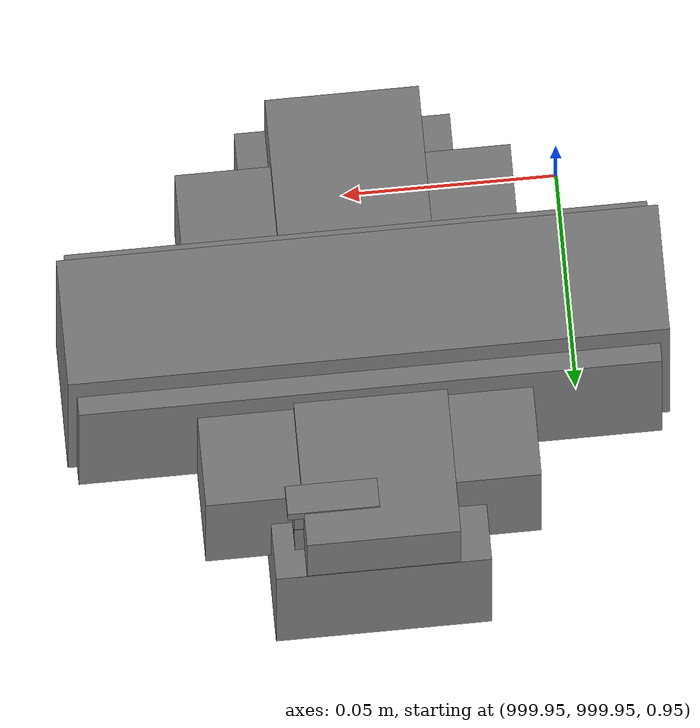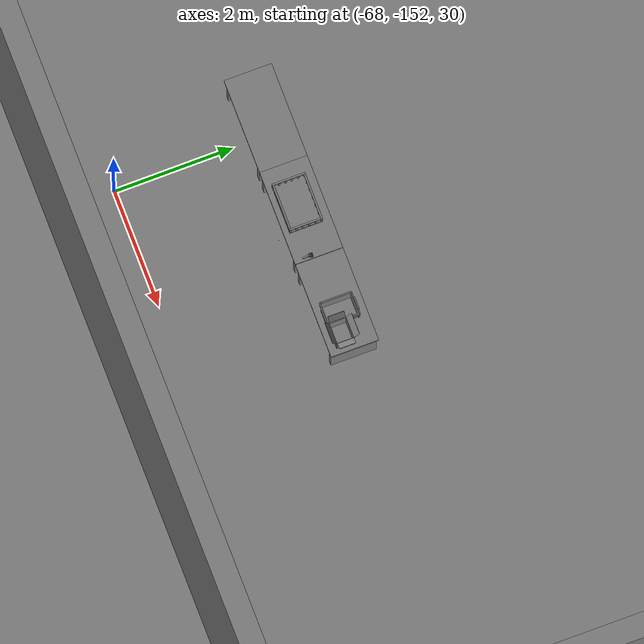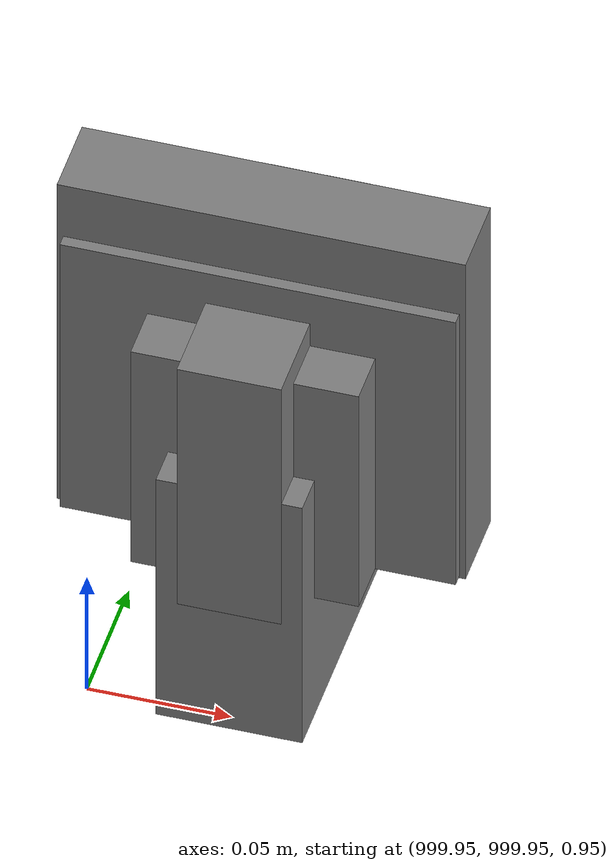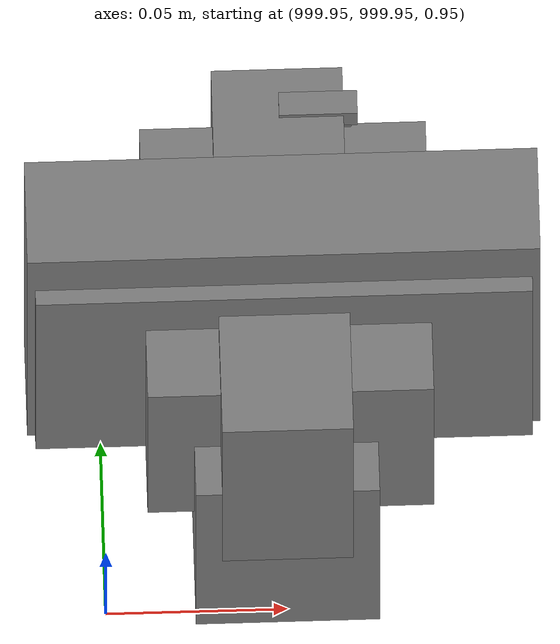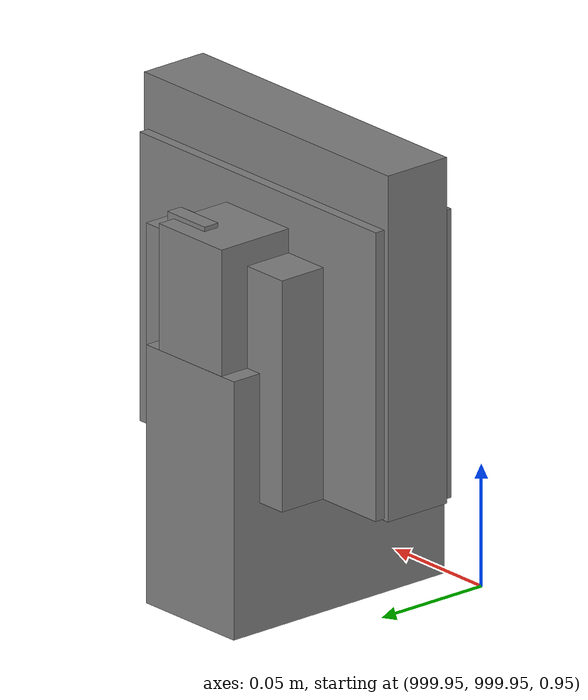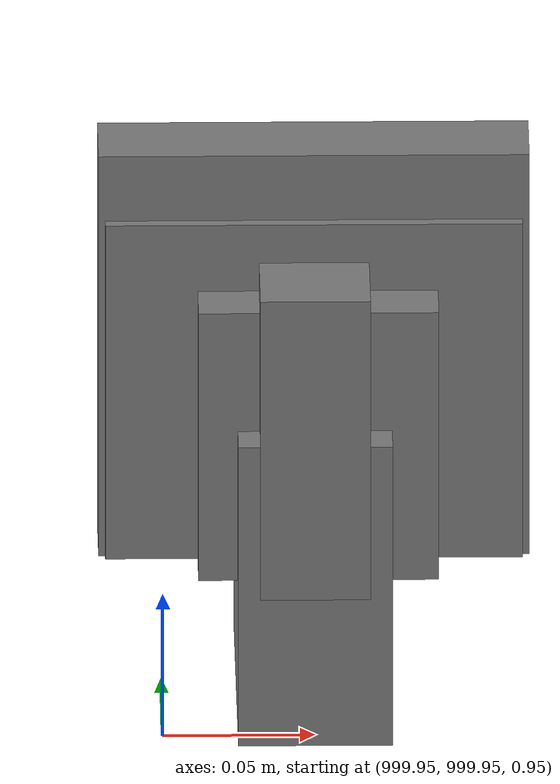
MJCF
<mujoco>
    <option gravity="0.000000000 0.000000000 -9.810000420" timestep="0.0049999999" integrator="implicitfast" density="1.225" viscosity="1.8000001e-05" noslip_iterations="10" iterations="100" sdf_iterations="50">
        <flag multiccd="disable"/>
    </option>
    <size memory="1000M"/>
    <compiler coordinate="local"/>
    <worldbody>
        <light cutoff="30" pos="0 1 1" dir="0 -1 -2"/>
        <light cutoff="30" pos="0 -1 1" dir="0 1 -2"/>
        <body pos="1000.000000000 999.999938965 1.000000000" euler="0.000000000 0.000000000 180.000000000" name="openloong_gripper_2f85_fix_base_usda_intelcore_i5">
            <geom contype="1" conaffinity="1" density="1000" type="box" material="" rgba="0.500000000 0.500000000 0.500000000 1.000000000" solimp="0.899999976 0.949999988 0.001000000" friction="1.000000000 0.005000000 0.000100000" solref="0.020000000 1.000000000" margin="0" condim="3" group="0" pos="0.000000000 0.000000000 0.051722717" quat="0.707106709 0.000000000 0.000000000 -0.707106769" size="0.052800000 0.018080002 0.052800000" name="openloong_gripper_2f85_fix_base_usda_geom_BBBBA1D3_30E7_46D5_83BF_B1B1D6643372"/>
            <freejoint name="openloong_gripper_2f85_fix_base_usda_intelcore_i5_joint"/>
            <site size="0.005000000 0.005000000 0.005000000" rgba="0.500000000 0.500000000 0.500000000 1.000000000" pos="0.000000000 0.000000000 0.000000000" quat="0.999961913 0.008726534 0.000000000 0.000000000" group="0" type="sphere" name="openloong_gripper_2f85_fix_base_usda_intelcore_i5site"/>
        </body>
        <body pos="-66.090927124 -149.022796631 31.169435501" euler="53.388214111 -78.519165039 82.427597046" mocap="true" name="spotlight2_SpotLight"/>
        <body pos="-65.859985352 -148.996490479 31.166822433" euler="101.490005493 19.338449478 15.209855080" mocap="true" name="spotlight6_SpotLight"/>
        <body pos="1000.000000000 1000.000000000 1.000000000" euler="0.000000000 0.000000000 180.000000000" name="openloong_gripper_2f85_fix_base_usda_wifi_box">
            <geom contype="1" conaffinity="1" density="1000" type="box" material="" rgba="0.500000000 0.500000000 0.500000000 1.000000000" solimp="0.899999976 0.949999988 0.001000000" friction="1.000000000 0.005000000 0.000100000" solref="0.020000000 1.000000000" margin="0" condim="3" group="0" pos="0.000000000 0.000000000 0.058978677" quat="0.000000000 0.000000047 0.000000000 1.000000000" size="0.068499997 0.018999999 0.059000000" name="openloong_gripper_2f85_fix_base_usda_geom_DB73FEE4_D299_4DA3_8F35_CD74D95670FE"/>
            <freejoint name="openloong_gripper_2f85_fix_base_usda_wifi_box_joint"/>
            <site size="0.005000000 0.005000000 0.005000000" rgba="0.500000000 0.500000000 0.500000000 1.000000000" pos="0.000000000 0.000000000 0.000000000" quat="0.999961913 0.008726500 0.000000000 0.000000000" group="0" type="sphere" name="openloong_gripper_2f85_fix_base_usda_wifi_boxsite"/>
        </body>
        <body pos="1000.000000000 1000.000000000 1.000000000" euler="0.000000000 0.000000000 180.000000000" name="openloong_gripper_2f85_fix_base_usda_cpu_fan">
            <geom contype="1" conaffinity="1" density="1000" type="box" material="" rgba="0.500000000 0.500000000 0.500000000 1.000000000" solimp="0.899999976 0.949999988 0.001000000" friction="1.000000000 0.005000000 0.000100000" solref="0.020000000 1.000000000" margin="0" condim="3" group="0" pos="0.000000000 0.000000000 0.070034981" quat="0.000000000 0.000000000 0.000000000 1.000000000" size="0.070700005 0.014699999 0.070700005" name="openloong_gripper_2f85_fix_base_usda_geom_D8EB0C9F_1BD7_4F25_8B97_FEC3EAD7AE5B"/>
            <freejoint name="openloong_gripper_2f85_fix_base_usda_cpu_fan_joint"/>
            <site size="0.005000000 0.005000000 0.005000000" rgba="0.500000000 0.500000000 0.500000000 1.000000000" pos="0.000000000 0.000000000 0.000000000" quat="0.999961913 0.008726535 0.000000000 0.000000000" group="0" type="sphere" name="openloong_gripper_2f85_fix_base_usda_cpu_fancsite"/>
        </body>
        <body pos="1000.000000000 1000.000000000 1.000000000" euler="0.000011953 0.000005123 -179.999984741" name="openloong_gripper_2f85_fix_base_usda_intel_box">
            <geom contype="1" conaffinity="1" density="1000" type="box" material="" rgba="0.500000000 0.500000000 0.500000000 1.000000000" solimp="0.899999976 0.949999988 0.001000000" friction="1.000000000 0.005000000 0.000100000" solref="0.020000000 1.000000000" margin="0" condim="3" group="0" pos="0.000000000 -0.000067139 0.000082284" quat="0.707106709 0.000000225 0.000000253 0.707106650" size="0.052800003 0.025300000 0.052800003" name="openloong_gripper_2f85_fix_base_usda_geom_20D65A65_5F75_41DB_8B6A_D2E92587D3C9"/>
            <freejoint name="openloong_gripper_2f85_fix_base_usda_intel_box_joint"/>
            <site size="0.005000000 0.005000000 0.005000000" rgba="0.500000000 0.500000000 0.500000000 1.000000000" pos="0.000000000 0.000000000 0.000000000" quat="0.999961913 0.008726500 0.000000000 0.000000000" group="0" type="sphere" name="openloong_gripper_2f85_fix_base_usda_intel_boxsite"/>
        </body>
        <body pos="-66.009407043 -149.299942017 31.164754868" euler="-110.916297913 87.186637878 -70.781349182" mocap="true" name="spotlight3_SpotLight"/>
        <body pos="1000.000000000 1000.000000000 1.000000000" euler="0.000000000 0.000000000 180.000000000" name="openloong_gripper_2f85_fix_base_usda_battery_01">
            <geom contype="1" conaffinity="1" density="1000" type="box" material="" rgba="0.500000000 0.500000000 0.500000000 1.000000000" solimp="0.899999976 0.949999988 0.001000000" friction="1.000000000 0.005000000 0.000100000" solref="0.020000000 1.000000000" margin="0" condim="3" group="0" pos="-0.011123657 -0.041940309 0.101691343" quat="1.000000000 0.000000000 0.000000000 0.000000000" size="0.010800000 0.003375000 0.004725000" name="openloong_gripper_2f85_fix_base_usda_geom_9C611488_4F6A_41FE_8B3E_6F0FC9D2A46A"/>
            <geom contype="1" conaffinity="1" density="1000" type="box" material="" rgba="0.500000000 0.500000000 0.500000000 1.000000000" solimp="0.899999976 0.949999988 0.001000000" friction="1.000000000 0.005000000 0.000100000" solref="0.020000000 1.000000000" margin="0" condim="3" group="0" pos="-0.010876465 -0.044247437 0.047066893" quat="0.998702705 -0.050920475 0.000000000 0.000000000" size="0.009450001 0.002700000 0.024975000" name="openloong_gripper_2f85_fix_base_usda_geom_3BEA2940_975A_4654_8D73_930403090DC0"/>
            <geom contype="1" conaffinity="1" density="1000" type="box" material="" rgba="0.500000000 0.500000000 0.500000000 1.000000000" solimp="0.899999976 0.949999988 0.001000000" friction="1.000000000 0.005000000 0.000100000" solref="0.020000000 1.000000000" margin="0" condim="3" group="0" pos="-0.001235962 -0.000659180 0.047381196" quat="1.000000000 0.000000000 0.000000000 0.000000000" size="0.039420001 0.039150000 0.047250003" name="openloong_gripper_2f85_fix_base_usda_geom_DFF39CAD_C7BB_4F3D_A0F1_B9FAB1E33584"/>
            <geom contype="1" conaffinity="1" density="1000" type="box" material="" rgba="0.500000000 0.500000000 0.500000000 1.000000000" solimp="0.899999976 0.949999988 0.001000000" friction="1.000000000 0.005000000 0.000100000" solref="0.020000000 1.000000000" margin="0" condim="3" group="0" pos="-0.010876465 -0.039138794 0.009851727" quat="1.000000000 0.000000000 0.000000000 0.000000000" size="0.009450001 0.010800000 0.013500000" name="openloong_gripper_2f85_fix_base_usda_geom_ECAE3774_4AB4_42AF_ABDE_5D968E666C19"/>
            <geom contype="1" conaffinity="1" density="1000" type="box" material="" rgba="0.500000000 0.500000000 0.500000000 1.000000000" solimp="0.899999976 0.949999988 0.001000000" friction="1.000000000 0.005000000 0.000100000" solref="0.020000000 1.000000000" margin="0" condim="3" group="0" pos="-0.010876465 -0.041528322 0.071508206" quat="1.000000000 0.000000000 0.000000000 0.000000000" size="0.009450001 0.002700000 0.027000001" name="openloong_gripper_2f85_fix_base_usda_geom_E1A3F757_F9B8_4F9D_AD3E_099EBD3A4080"/>
            <freejoint name="openloong_gripper_2f85_fix_base_usda_battery_01_joint"/>
            <site size="0.005000000 0.005000000 0.005000000" rgba="0.500000000 0.500000000 0.500000000 1.000000000" pos="0.000000000 0.000000000 0.000000000" quat="0.999961913 0.008726500 0.000000000 0.000000000" group="0" type="sphere" name="openloong_gripper_2f85_fix_base_usda_battery_01site"/>
        </body>
        <body pos="-64.866622925 -149.383972168 30.183746338" euler="89.999984741 89.999946594 0.000000000" name="openloong_gripper_2f85_fix_base_usda_bluebox_01">
            <geom contype="1" conaffinity="1" density="1000" type="box" material="" rgba="0.500000000 0.500000000 0.500000000 1.000000000" solimp="0.899999976 0.949999988 0.001000000" friction="1.000000000 0.005000000 0.000100000" solref="0.020000000 1.000000000" margin="0" condim="3" group="0" pos="0.276580811 0.187225342 0.000068665" quat="0.707106948 0.000077471 0.707106352 0.000077486" size="0.100000001 0.057999998 0.010000000" name="openloong_gripper_2f85_fix_base_usda_geom_2083E90D_57A8_4792_812E_F72AF3B7757D"/>
            <geom contype="1" conaffinity="1" density="1000" type="box" material="" rgba="0.500000000 0.500000000 0.500000000 1.000000000" solimp="0.899999976 0.949999988 0.001000000" friction="1.000000000 0.005000000 0.000100000" solref="0.020000000 1.000000000" margin="0" condim="3" group="0" pos="0.000000000 0.002883911 0.000000000" quat="0.999999881 0.000000000 0.000000000 0.000000000" size="0.254000008 0.003000000 0.172000006" name="openloong_gripper_2f85_fix_base_usda_geom_2849D219_03A9_45E1_B3C5_2264F7A68075"/>
            <geom contype="1" conaffinity="1" density="1000" type="box" material="" rgba="0.500000000 0.500000000 0.500000000 1.000000000" solimp="0.899999976 0.949999988 0.001000000" friction="1.000000000 0.005000000 0.000100000" solref="0.020000000 1.000000000" margin="0" condim="3" group="0" pos="0.000000000 0.124874115 0.173484802" quat="0.999796331 0.020176515 -0.000000015 0.000000030" size="0.259999990 0.119999997 0.007000000" name="openloong_gripper_2f85_fix_base_usda_geom_A5CBF77D_95D2_4549_8B87_686A32A7295D"/>
            <geom contype="1" conaffinity="1" density="1000" type="box" material="" rgba="0.500000000 0.500000000 0.500000000 1.000000000" solimp="0.899999976 0.949999988 0.001000000" friction="1.000000000 0.005000000 0.000100000" solref="0.020000000 1.000000000" margin="0" condim="3" group="0" pos="0.000000000 0.124874115 -0.173469543" quat="0.999796331 -0.020176545 -0.000000015 0.000000000" size="0.259999990 0.119999997 0.007000000" name="openloong_gripper_2f85_fix_base_usda_geom_E3FDB78B_D31F_4B40_9EC3_97E432586B7D"/>
            <geom contype="1" conaffinity="1" density="1000" type="box" material="" rgba="0.500000000 0.500000000 0.500000000 1.000000000" solimp="0.899999976 0.949999988 0.001000000" friction="1.000000000 0.005000000 0.000100000" solref="0.020000000 1.000000000" margin="0" condim="3" group="0" pos="0.000000000 0.214008331 0.188980103" quat="0.999912977 0.013176724 0.000000015 0.000000000" size="0.259999990 0.029999999 0.012500000" name="openloong_gripper_2f85_fix_base_usda_geom_267E5F4D_AF11_4FD2_8C52_DC28817E2D46"/>
            <geom contype="1" conaffinity="1" density="1000" type="box" material="" rgba="0.500000000 0.500000000 0.500000000 1.000000000" solimp="0.899999976 0.949999988 0.001000000" friction="1.000000000 0.005000000 0.000100000" solref="0.020000000 1.000000000" margin="0" condim="3" group="0" pos="-0.258361816 0.125289917 0.001876831" quat="0.702796936 -0.020792112 0.710783124 0.020769298" size="0.189999998 0.119999997 0.009000000" name="openloong_gripper_2f85_fix_base_usda_geom_24B32EEA_EC02_4603_8E3A_5D9163C6D0BC"/>
            <geom contype="1" conaffinity="1" density="1000" type="box" material="" rgba="0.500000000 0.500000000 0.500000000 1.000000000" solimp="0.899999976 0.949999988 0.001000000" friction="1.000000000 0.005000000 0.000100000" solref="0.020000000 1.000000000" margin="0" condim="3" group="0" pos="0.000000000 0.214008331 -0.188980103" quat="0.999912977 -0.013176769 0.000000030 0.000000015" size="0.259999990 0.029999999 0.012500000" name="openloong_gripper_2f85_fix_base_usda_geom_38AA4BAA_C93C_4C8C_B0B2_5008360E9353"/>
            <geom contype="1" conaffinity="1" density="1000" type="box" material="" rgba="0.500000000 0.500000000 0.500000000 1.000000000" solimp="0.899999976 0.949999988 0.001000000" friction="1.000000000 0.005000000 0.000100000" solref="0.020000000 1.000000000" margin="0" condim="3" group="0" pos="-0.276611328 0.187225342 0.000068665" quat="0.707106650 0.000077441 0.707106709 0.000077456" size="0.100000001 0.057999998 0.010000000" name="openloong_gripper_2f85_fix_base_usda_geom_16FEB99E_B0B3_422F_A7D0_E46B0C6F983A"/>
            <geom contype="1" conaffinity="1" density="1000" type="box" material="" rgba="0.500000000 0.500000000 0.500000000 1.000000000" solimp="0.899999976 0.949999988 0.001000000" friction="1.000000000 0.005000000 0.000100000" solref="0.020000000 1.000000000" margin="0" condim="3" group="0" pos="0.258331299 0.125289917 0.001876831" quat="0.702851415 0.018856421 0.710823774 -0.019329369" size="0.189999998 0.119999997 0.009000000" name="openloong_gripper_2f85_fix_base_usda_geom_36FEB4BF_ECD8_4F03_A3A9_55B5C3C84FCA"/>
            <freejoint name="openloong_gripper_2f85_fix_base_usda_bluebox_01_joint"/>
            <site size="0.005000000 0.005000000 0.005000000" rgba="0.500000000 0.500000000 0.500000000 1.000000000" pos="0.000000000 0.000000000 0.000000000" quat="0.999961913 0.008726534 0.000000000 0.000000000" group="0" type="sphere" name="openloong_gripper_2f85_fix_base_usda_bluebox_01site"/>
        </body>
        <body pos="-64.496299744 -149.491867065 30.235729218" euler="0.000000000 0.000000000 89.999946594" name="openloong_gripper_2f85_fix_base_usda_cardboardbox_01">
            <geom contype="1" conaffinity="1" density="1000" type="box" material="" rgba="0.500000000 0.500000000 0.500000000 1.000000000" solimp="0.899999976 0.949999988 0.001000000" friction="1.000000000 0.005000000 0.000100000" solref="0.020000000 1.000000000" margin="0" condim="3" group="0" pos="-0.003166199 -0.004086494 0.005052090" quat="1.000000000 0.000000000 0.000000000 0.000000000" size="0.142499998 0.177500010 0.005000000" name="openloong_gripper_2f85_fix_base_usda_geom_3AC043BD_2D24_4A9A_A91B_0AC7B7CDB16A"/>
            <geom contype="1" conaffinity="1" density="1000" type="box" material="" rgba="0.500000000 0.500000000 0.500000000 1.000000000" solimp="0.899999976 0.949999988 0.001000000" friction="1.000000000 0.005000000 0.000100000" solref="0.020000000 1.000000000" margin="0" condim="3" group="0" pos="-0.003166199 0.170316696 0.150570869" quat="1.000000000 0.000000000 0.000000000 0.000000000" size="0.142499998 0.005000000 0.149999991" name="openloong_gripper_2f85_fix_base_usda_geom_5C9CED94_F3E5_4ED2_BA3B_0A5C3107E78B"/>
            <geom contype="1" conaffinity="1" density="1000" type="box" material="" rgba="0.500000000 0.500000000 0.500000000 1.000000000" solimp="0.899999976 0.949999988 0.001000000" friction="1.000000000 0.005000000 0.000100000" solref="0.020000000 1.000000000" margin="0" condim="3" group="0" pos="-0.147399902 -0.005307198 0.150570869" quat="1.000000000 0.000000000 0.000000000 0.000000000" size="0.005000000 0.177500010 0.149999991" name="openloong_gripper_2f85_fix_base_usda_geom_EF6B3CF7_9F0D_4632_88F1_723430B27AD2"/>
            <geom contype="1" conaffinity="1" density="1000" type="box" material="" rgba="0.500000000 0.500000000 0.500000000 1.000000000" solimp="0.899999976 0.949999988 0.001000000" friction="1.000000000 0.005000000 0.000100000" solref="0.020000000 1.000000000" margin="0" condim="3" group="0" pos="0.140275955 -0.005307198 0.150570869" quat="1.000000000 0.000000000 0.000000000 0.000000000" size="0.005000000 0.177500010 0.149999991" name="openloong_gripper_2f85_fix_base_usda_geom_C0C580B3_39AA_416D_9F24_EE9DAD1A64D1"/>
            <geom contype="1" conaffinity="1" density="1000" type="box" material="" rgba="0.500000000 0.500000000 0.500000000 1.000000000" solimp="0.899999976 0.949999988 0.001000000" friction="1.000000000 0.005000000 0.000100000" solref="0.020000000 1.000000000" margin="0" condim="3" group="0" pos="-0.003166199 -0.181550980 0.150570869" quat="1.000000000 0.000000000 0.000000000 0.000000000" size="0.142499998 0.005000000 0.149999991" name="openloong_gripper_2f85_fix_base_usda_geom_5373072B_C9E1_42B6_94A1_B0775FDF3EB3"/>
            <freejoint name="openloong_gripper_2f85_fix_base_usda_cardboardbox_01_joint"/>
            <site size="0.005000000 0.005000000 0.005000000" rgba="0.500000000 0.500000000 0.500000000 1.000000000" pos="0.000000000 0.000000000 0.000000000" quat="0.999961913 0.008726535 0.000000000 0.000000000" group="0" type="sphere" name="openloong_gripper_2f85_fix_base_usda_site_FC3A319D_7DEE_4987_8B3F_4B804A613FD9"/>
            <body pos="0.139160156 -0.004048347 0.301930904" euler="-179.999954224 49.383502960 179.999954224" name="openloong_gripper_2f85_fix_base_usda_A1_006">
                <geom contype="1" conaffinity="1" density="1000" type="box" material="" rgba="0.500000000 0.500000000 0.500000000 1.000000000" solimp="0.899999976 0.949999988 0.001000000" friction="1.000000000 0.005000000 0.000100000" solref="0.020000000 1.000000000" margin="0" condim="3" group="0" pos="-0.071587563 0.000009537 0.001745224" quat="0.999999881 0.000000000 0.000000000 0.000000000" size="0.071249999 0.179999992 0.002500000" name="openloong_gripper_2f85_fix_base_usda_geom_B27DA1D3_2396_4269_991D_3A5DE4942B9A"/>
                <joint armature="0" stiffness="0.07" damping="0.0099999998" axis="0.000000 1.000000 0.000000" type="hinge" name="openloong_gripper_2f85_fix_base_usda_A1_006"/>
            </body>
            <body pos="-0.145902634 -0.004086494 0.301938057" euler="-180.000000000 -60.000011444 -180.000000000" name="openloong_gripper_2f85_fix_base_usda_A2_006">
                <geom contype="1" conaffinity="1" density="1000" type="box" material="" rgba="0.500000000 0.500000000 0.500000000 1.000000000" solimp="0.899999976 0.949999988 0.001000000" friction="1.000000000 0.005000000 0.000100000" solref="0.020000000 1.000000000" margin="0" condim="3" group="0" pos="0.071268082 0.000009537 0.002717972" quat="0.000002921 0.000000000 -0.000000030 0.999999881" size="0.071249999 0.179999992 0.002500000" name="openloong_gripper_2f85_fix_base_usda_geom_CF46911B_37E2_43A0_BF69_12AAFE349B95"/>
                <joint armature="0" stiffness="0.07" damping="0.0099999998" axis="0.000000 1.000000 0.000000" type="hinge" name="openloong_gripper_2f85_fix_base_usda_A2_006"/>
            </body>
            <body pos="-0.003385544 0.175991058 0.301930904" euler="-125.858116150 -0.000004561 0.000002331" name="openloong_gripper_2f85_fix_base_usda_B2_006">
                <geom contype="1" conaffinity="1" density="1000" type="box" material="" rgba="0.500000000 0.500000000 0.500000000 1.000000000" solimp="0.899999976 0.949999988 0.001000000" friction="1.000000000 0.005000000 0.000100000" solref="0.020000000 1.000000000" margin="0" condim="3" group="0" pos="0.000009537 -0.070939064 -0.002470016" quat="0.999614120 0.027776197 -0.000000015 0.000000030" size="0.137500003 0.064999998 0.005000000" name="openloong_gripper_2f85_fix_base_usda_geom_91C5CDBA_E599_417B_91E2_DA91D4DDDA54"/>
                <joint armature="0" stiffness="0.07" damping="0.0099999998" axis="1.000000 0.000000 0.000000" type="hinge" name="openloong_gripper_2f85_fix_base_usda_B2_006"/>
            </body>
            <body pos="-0.003385544 -0.184140205 0.301938057" euler="147.805557251 0.000000000 0.000000000" name="openloong_gripper_2f85_fix_base_usda_B1_006">
                <geom contype="1" conaffinity="1" density="1000" type="box" material="" rgba="0.500000000 0.500000000 0.500000000 1.000000000" solimp="0.899999976 0.949999988 0.001000000" friction="1.000000000 0.005000000 0.000100000" solref="0.020000000 1.000000000" margin="0" condim="3" group="0" pos="-0.000028610 0.070202351 -0.002703667" quat="0.999614179 -0.027776167 0.000000000 0.000000000" size="0.137500003 0.064999998 0.005000000" name="openloong_gripper_2f85_fix_base_usda_geom_48525AA6_B31A_48AB_A080_68D27D8EAAC4"/>
                <joint armature="0" stiffness="0.07" damping="0.0099999998" axis="1.000000 0.000000 0.000000" type="hinge" name="openloong_gripper_2f85_fix_base_usda_B1_006"/>
            </body>
        </body>
        <body pos="-65.882858276 -149.481979370 30.229999542" euler="-64.487716675 0.000000000 0.000000000" name="openloong_gripper_2f85_fix_base_usda_Barcode">
            <geom contype="1" conaffinity="1" density="1000" type="box" material="" rgba="0.500000000 0.500000000 0.500000000 1.000000000" solimp="0.899999976 0.949999988 0.001000000" friction="1.000000000 0.005000000 0.000100000" solref="0.020000000 1.000000000" margin="0" condim="3" group="0" pos="0.000000000 0.013038635 0.001419067" quat="0.000000000 0.000000000 0.000000000 1.000000119" size="0.034000002 0.010000000 0.017999999" name="openloong_gripper_2f85_fix_base_usda_geom_A184D324_1C46_411A_B4AB_94A343844330"/>
            <geom contype="1" conaffinity="1" density="1000" type="box" material="" rgba="0.500000000 0.500000000 0.500000000 1.000000000" solimp="0.899999976 0.949999988 0.001000000" friction="1.000000000 0.005000000 0.000100000" solref="0.020000000 1.000000000" margin="0" condim="3" group="0" pos="0.000000000 -0.035301208 -0.007095337" quat="0.000000000 0.000000000 -0.043619365 0.999048233" size="0.028999999 0.010000000 0.020000000" name="openloong_gripper_2f85_fix_base_usda_geom_53D0DECD_0AC0_4046_847B_366585D61245"/>
            <geom contype="1" conaffinity="1" density="1000" type="box" material="" rgba="0.500000000 0.500000000 0.500000000 1.000000000" solimp="0.899999976 0.949999988 0.001000000" friction="1.000000000 0.005000000 0.000100000" solref="0.020000000 1.000000000" margin="0" condim="3" group="0" pos="0.000000000 -0.043411255 -0.011749268" quat="0.922262907 0.386563420 0.000000000 0.000000000" size="0.026000001 0.010000000 0.020000000" name="openloong_gripper_2f85_fix_base_usda_geom_A66D9A19_581B_4CA9_81EB_B6994EB6875B"/>
            <geom contype="1" conaffinity="1" density="1000" type="box" material="" rgba="0.500000000 0.500000000 0.500000000 1.000000000" solimp="0.899999976 0.949999988 0.001000000" friction="1.000000000 0.005000000 0.000100000" solref="0.020000000 1.000000000" margin="0" condim="3" group="0" pos="0.000000000 -0.016967773 -0.031860352" quat="0.000000000 0.000000000 0.000000000 1.000000119" size="0.008000000 0.010000000 0.013000000" name="openloong_gripper_2f85_fix_base_usda_geom_5A082494_2E4F_4D17_AAC5_51A68E9A1D91"/>
            <geom contype="1" conaffinity="1" density="1000" type="box" material="" rgba="0.500000000 0.500000000 0.500000000 1.000000000" solimp="0.899999976 0.949999988 0.001000000" friction="1.000000000 0.005000000 0.000100000" solref="0.020000000 1.000000000" margin="0" condim="3" group="0" pos="0.000000000 -0.001869202 0.000312805" quat="0.953716993 0.300705761 0.000000000 0.000000000" size="0.032000002 0.010000000 0.018999999" name="openloong_gripper_2f85_fix_base_usda_geom_E6EC8E33_FA56_4400_88A0_E01C4CF1D6BB"/>
            <geom contype="1" conaffinity="1" density="1000" type="box" material="" rgba="0.500000000 0.500000000 0.500000000 1.000000000" solimp="0.899999976 0.949999988 0.001000000" friction="1.000000000 0.005000000 0.000100000" solref="0.020000000 1.000000000" margin="0" condim="3" group="0" pos="0.000000000 -0.019531250 -0.003173828" quat="0.953716993 0.300705761 0.000000000 0.000000000" size="0.030999999 0.010000000 0.020000000" name="openloong_gripper_2f85_fix_base_usda_geom_81DEB266_BF14_475E_BEE7_7EEC32FB3488"/>
            <geom contype="1" conaffinity="1" density="1000" type="box" material="" rgba="0.500000000 0.500000000 0.500000000 1.000000000" solimp="0.899999976 0.949999988 0.001000000" friction="1.000000000 0.005000000 0.000100000" solref="0.020000000 1.000000000" margin="0" condim="3" group="0" pos="0.000000000 -0.035301208 -0.007095337" quat="0.953716993 0.300705761 0.000000000 0.000000000" size="0.028999999 0.010000000 0.020000000" name="openloong_gripper_2f85_fix_base_usda_geom_94C52194_864F_4885_89F6_46140B740226"/>
            <geom contype="1" conaffinity="1" density="1000" type="box" material="" rgba="0.500000000 0.500000000 0.500000000 1.000000000" solimp="0.899999976 0.949999988 0.001000000" friction="1.000000000 0.005000000 0.000100000" solref="0.020000000 1.000000000" margin="0" condim="3" group="0" pos="0.000000000 -0.042617798 -0.071121216" quat="0.000000000 0.000000000 0.000000000 1.000000119" size="0.013000000 0.021000000 0.059999999" name="openloong_gripper_2f85_fix_base_usda_geom_1EC071E5_DCCD_4EA3_9454_456941119E33"/>
            <freejoint name="openloong_gripper_2f85_fix_base_usda_Barcode_joint"/>
            <site size="0.005000000 0.005000000 0.005000000" rgba="0.500000000 0.500000000 0.500000000 1.000000000" pos="0.000000000 0.000000000 0.000000000" quat="1.000000000 0.000000000 0.000000000 0.000000000" group="0" type="sphere" name="openloong_gripper_2f85_fix_base_usda_Barcode_site"/>
        </body>
        <body pos="-66.745018005 -149.392349243 30.184000015" euler="0.000000000 0.000000000 89.999946594" name="[22331825788697]_Basket_01">
            <geom contype="1" conaffinity="1" density="1000" type="box" material="" rgba="0.500000000 0.500000000 0.500000000 1.000000000" solimp="0.899999976 0.949999988 0.001000000" friction="1.000000000 0.005000000 0.000100000" solref="0.020000000 1.000000000" margin="0" condim="3" group="0" pos="-0.052425385 0.389207840 0.089787483" quat="0.707107008 0.000000000 0.000000000 0.707106411" size="0.014249999 0.014249999 0.059999999" name="[22331825788697]_geom_67ADA3E9_A1E7_4796_B860_389271C49AE0"/>
            <geom contype="1" conaffinity="1" density="1000" type="box" material="" rgba="0.500000000 0.500000000 0.500000000 1.000000000" solimp="0.899999976 0.949999988 0.001000000" friction="1.000000000 0.005000000 0.000100000" solref="0.020000000 1.000000000" margin="0" condim="3" group="0" pos="0.264015198 -0.133043289 0.089787483" quat="0.707107008 0.000000000 0.000000000 0.707106411" size="0.014249999 0.014249999 0.059999999" name="[22331825788697]_geom_7D2365EF_447F_4537_A421_AA6A1E4B5ED3"/>
            <geom contype="1" conaffinity="1" density="1000" type="box" material="" rgba="0.500000000 0.500000000 0.500000000 1.000000000" solimp="0.899999976 0.949999988 0.001000000" friction="1.000000000 0.005000000 0.000100000" solref="0.020000000 1.000000000" margin="0" condim="3" group="0" pos="-0.264015198 -0.265548706 0.089793205" quat="0.707107008 0.000000000 0.000000000 0.707106411" size="0.014249999 0.014249999 0.059999999" name="[22331825788697]_geom_2FB7372C_22AF_41B8_A166_C18CE79CD2B5"/>
            <geom contype="1" conaffinity="1" density="1000" type="box" material="" rgba="0.500000000 0.500000000 0.500000000 1.000000000" solimp="0.899999976 0.949999988 0.001000000" friction="1.000000000 0.005000000 0.000100000" solref="0.020000000 1.000000000" margin="0" condim="3" group="0" pos="-0.160263062 -0.389322281 0.089793205" quat="0.707107008 0.000000000 0.000000000 0.707106411" size="0.014249999 0.014249999 0.059999999" name="[22331825788697]_geom_A05E9B94_C996_4EBD_81A5_347B0828B359"/>
            <geom contype="1" conaffinity="1" density="1000" type="box" material="" rgba="0.500000000 0.500000000 0.500000000 1.000000000" solimp="0.899999976 0.949999988 0.001000000" friction="1.000000000 0.005000000 0.000100000" solref="0.020000000 1.000000000" margin="0" condim="3" group="0" pos="0.162265778 -0.389322281 0.089787483" quat="0.707107008 0.000000000 0.000000000 0.707106411" size="0.014249999 0.014249999 0.059999999" name="[22331825788697]_geom_AB836936_A1D2_4F16_8EAE_21B183914179"/>
            <geom contype="1" conaffinity="1" density="1000" type="box" material="" rgba="0.500000000 0.500000000 0.500000000 1.000000000" solimp="0.899999976 0.949999988 0.001000000" friction="1.000000000 0.005000000 0.000100000" solref="0.020000000 1.000000000" margin="0" condim="3" group="0" pos="0.264015198 0.389207840 0.089787483" quat="0.707107008 0.000000000 0.000000000 0.707106411" size="0.014249999 0.014249999 0.059999999" name="[22331825788697]_geom_D17DF048_2840_44CA_B746_BD472C14A636"/>
            <geom contype="1" conaffinity="1" density="1000" type="box" material="" rgba="0.500000000 0.500000000 0.500000000 1.000000000" solimp="0.899999976 0.949999988 0.001000000" friction="1.000000000 0.005000000 0.000100000" solref="0.020000000 1.000000000" margin="0" condim="3" group="0" pos="-0.264015198 -0.133043289 0.089793205" quat="0.707107008 0.000000000 0.000000000 0.707106411" size="0.014249999 0.014249999 0.059999999" name="[22331825788697]_geom_36ADF48A_BE6D_4544_BC34_69EB4BFE3616"/>
            <geom contype="1" conaffinity="1" density="1000" type="box" material="" rgba="0.500000000 0.500000000 0.500000000 1.000000000" solimp="0.899999976 0.949999988 0.001000000" friction="1.000000000 0.005000000 0.000100000" solref="0.020000000 1.000000000" margin="0" condim="3" group="0" pos="-0.264026642 0.269256592 0.089793205" quat="0.707107008 0.000000000 0.000000000 0.707106411" size="0.014249999 0.014249999 0.059999999" name="[22331825788697]_geom_148C74F4_2BDA_4C89_894F_F02EA40693C5"/>
            <geom contype="1" conaffinity="1" density="1000" type="box" material="" rgba="0.500000000 0.500000000 0.500000000 1.000000000" solimp="0.899999976 0.949999988 0.001000000" friction="1.000000000 0.005000000 0.000100000" solref="0.020000000 1.000000000" margin="0" condim="3" group="0" pos="0.054462433 0.389207840 0.089787483" quat="0.707107008 0.000000000 0.000000000 0.707106411" size="0.014249999 0.014249999 0.059999999" name="[22331825788697]_geom_9D19682C_1D0B_421D_92D8_3C1581541969"/>
            <geom contype="1" conaffinity="1" density="1000" type="box" material="" rgba="0.500000000 0.500000000 0.500000000 1.000000000" solimp="0.899999976 0.949999988 0.001000000" friction="1.000000000 0.005000000 0.000100000" solref="0.020000000 1.000000000" margin="0" condim="3" group="0" pos="0.054462433 -0.389322281 0.089787483" quat="0.707107008 0.000000000 0.000000000 0.707106411" size="0.014249999 0.014249999 0.059999999" name="[22331825788697]_geom_092F6F2D_3662_43C2_91E9_823AD196D02C"/>
            <geom contype="1" conaffinity="1" density="1000" type="box" material="" rgba="0.500000000 0.500000000 0.500000000 1.000000000" solimp="0.899999976 0.949999988 0.001000000" friction="1.000000000 0.005000000 0.000100000" solref="0.020000000 1.000000000" margin="0" condim="3" group="0" pos="0.264015198 0.269256592 0.089793205" quat="0.707107008 0.000000000 0.000000000 0.707106411" size="0.014249999 0.014249999 0.059999999" name="[22331825788697]_geom_D8548C0D_BE34_4F52_A598_09FCAF014DA4"/>
            <geom contype="1" conaffinity="1" density="1000" type="box" material="" rgba="0.500000000 0.500000000 0.500000000 1.000000000" solimp="0.899999976 0.949999988 0.001000000" friction="1.000000000 0.005000000 0.000100000" solref="0.020000000 1.000000000" margin="0" condim="3" group="0" pos="0.264015198 -0.389322281 0.089787483" quat="0.707107008 0.000000000 0.000000000 0.707106411" size="0.014249999 0.014249999 0.059999999" name="[22331825788697]_geom_A8E64666_8014_42E7_82E8_5EB40BDF9FF3"/>
            <geom contype="1" conaffinity="1" density="1000" type="box" material="" rgba="0.500000000 0.500000000 0.500000000 1.000000000" solimp="0.899999976 0.949999988 0.001000000" friction="1.000000000 0.005000000 0.000100000" solref="0.020000000 1.000000000" margin="0" condim="3" group="0" pos="0.000000000 0.000000000 0.015998840" quat="0.707107008 0.000000000 0.000000000 0.707106411" size="0.403499991 0.279000014 0.015750000" name="[22331825788697]_geom_A9C39624_1452_4566_A726_ED3E97559EAA"/>
            <geom contype="1" conaffinity="1" density="1000" type="box" material="" rgba="0.500000000 0.500000000 0.500000000 1.000000000" solimp="0.899999976 0.949999988 0.001000000" friction="1.000000000 0.005000000 0.000100000" solref="0.020000000 1.000000000" margin="0" condim="3" group="0" pos="0.000000000 -0.389476776 0.163619041" quat="0.707107008 0.000000000 0.000000000 0.707106411" size="0.015000000 0.277500004 0.015750000" name="[22331825788697]_geom_FE609729_3407_4400_9A74_CD06956BEA78"/>
            <geom contype="1" conaffinity="1" density="1000" type="box" material="" rgba="0.500000000 0.500000000 0.500000000 1.000000000" solimp="0.899999976 0.949999988 0.001000000" friction="1.000000000 0.005000000 0.000100000" solref="0.020000000 1.000000000" margin="0" condim="3" group="0" pos="0.162265778 0.389207840 0.089787483" quat="0.707107008 0.000000000 0.000000000 0.707106411" size="0.014249999 0.014249999 0.059999999" name="[22331825788697]_geom_B3695A3B_B7FA_419C_B841_648E381F1196"/>
            <geom contype="1" conaffinity="1" density="1000" type="box" material="" rgba="0.500000000 0.500000000 0.500000000 1.000000000" solimp="0.899999976 0.949999988 0.001000000" friction="1.000000000 0.005000000 0.000100000" solref="0.020000000 1.000000000" margin="0" condim="3" group="0" pos="0.000000000 0.389471054 0.163619041" quat="0.707107008 0.000000000 0.000000000 0.707106411" size="0.015000000 0.277500004 0.015750000" name="[22331825788697]_geom_FCE627AE_BE90_4899_9ACC_0415ACA5B508"/>
            <geom contype="1" conaffinity="1" density="1000" type="box" material="" rgba="0.500000000 0.500000000 0.500000000 1.000000000" solimp="0.899999976 0.949999988 0.001000000" friction="1.000000000 0.005000000 0.000100000" solref="0.020000000 1.000000000" margin="0" condim="3" group="0" pos="-0.263511658 0.000000000 0.163619041" quat="0.707107008 0.000000000 0.000000000 0.707106411" size="0.403499991 0.015000000 0.015750000" name="[22331825788697]_geom_520594BA_7D37_45B5_8A06_A2356A1E7D0B"/>
            <geom contype="1" conaffinity="1" density="1000" type="box" material="" rgba="0.500000000 0.500000000 0.500000000 1.000000000" solimp="0.899999976 0.949999988 0.001000000" friction="1.000000000 0.005000000 0.000100000" solref="0.020000000 1.000000000" margin="0" condim="3" group="0" pos="-0.264015198 0.141334534 0.089793205" quat="0.707107008 0.000000000 0.000000000 0.707106411" size="0.014249999 0.014249999 0.059999999" name="[22331825788697]_geom_13AABA24_A213_4674_B388_C908506D84D5"/>
            <geom contype="1" conaffinity="1" density="1000" type="box" material="" rgba="0.500000000 0.500000000 0.500000000 1.000000000" solimp="0.899999976 0.949999988 0.001000000" friction="1.000000000 0.005000000 0.000100000" solref="0.020000000 1.000000000" margin="0" condim="3" group="0" pos="0.264015198 -0.265548706 0.089787483" quat="0.707107008 0.000000000 0.000000000 0.707106411" size="0.014249999 0.014249999 0.059999999" name="[22331825788697]_geom_45F3C563_53E5_43FC_A57D_A6FAF254AF49"/>
            <geom contype="1" conaffinity="1" density="1000" type="box" material="" rgba="0.500000000 0.500000000 0.500000000 1.000000000" solimp="0.899999976 0.949999988 0.001000000" friction="1.000000000 0.005000000 0.000100000" solref="0.020000000 1.000000000" margin="0" condim="3" group="0" pos="-0.160263062 0.389207840 0.089787483" quat="0.707107008 0.000000000 0.000000000 0.707106411" size="0.014249999 0.014249999 0.059999999" name="[22331825788697]_geom_DD41D29F_700D_4084_919C_50A3B7011180"/>
            <geom contype="1" conaffinity="1" density="1000" type="box" material="" rgba="0.500000000 0.500000000 0.500000000 1.000000000" solimp="0.899999976 0.949999988 0.001000000" friction="1.000000000 0.005000000 0.000100000" solref="0.020000000 1.000000000" margin="0" condim="3" group="0" pos="-0.052425385 -0.389322281 0.089787483" quat="0.707107008 0.000000000 0.000000000 0.707106411" size="0.014249999 0.014249999 0.059999999" name="[22331825788697]_geom_D184EBA5_C5F8_456E_8D88_F5C413036843"/>
            <geom contype="1" conaffinity="1" density="1000" type="box" material="" rgba="0.500000000 0.500000000 0.500000000 1.000000000" solimp="0.899999976 0.949999988 0.001000000" friction="1.000000000 0.005000000 0.000100000" solref="0.020000000 1.000000000" margin="0" condim="3" group="0" pos="-0.264026642 -0.389322281 0.089793205" quat="0.707107008 0.000000000 0.000000000 0.707106411" size="0.014249999 0.014249999 0.059999999" name="[22331825788697]_geom_51878E1A_2B15_484D_A11A_57DAA7A152B0"/>
            <geom contype="1" conaffinity="1" density="1000" type="box" material="" rgba="0.500000000 0.500000000 0.500000000 1.000000000" solimp="0.899999976 0.949999988 0.001000000" friction="1.000000000 0.005000000 0.000100000" solref="0.020000000 1.000000000" margin="0" condim="3" group="0" pos="0.264015198 0.141334534 0.089787483" quat="0.707107008 0.000000000 0.000000000 0.707106411" size="0.014249999 0.014249999 0.059999999" name="[22331825788697]_geom_7D5D1FF1_C9A6_4DC3_B04A_91A4C3C76328"/>
            <geom contype="1" conaffinity="1" density="1000" type="box" material="" rgba="0.500000000 0.500000000 0.500000000 1.000000000" solimp="0.899999976 0.949999988 0.001000000" friction="1.000000000 0.005000000 0.000100000" solref="0.020000000 1.000000000" margin="0" condim="3" group="0" pos="-0.264015198 0.389207840 0.089793205" quat="0.707107008 0.000000000 0.000000000 0.707106411" size="0.014249999 0.014249999 0.059999999" name="[22331825788697]_geom_01B5406A_501D_4AE2_A73A_9E071438751C"/>
            <geom contype="1" conaffinity="1" density="1000" type="box" material="" rgba="0.500000000 0.500000000 0.500000000 1.000000000" solimp="0.899999976 0.949999988 0.001000000" friction="1.000000000 0.005000000 0.000100000" solref="0.020000000 1.000000000" margin="0" condim="3" group="0" pos="0.264015198 0.004480362 0.089787483" quat="0.707107008 0.000000000 0.000000000 0.707106411" size="0.014249999 0.014249999 0.059999999" name="[22331825788697]_geom_72F9668E_6929_41C5_99FE_E8F9D26294C6"/>
            <geom contype="1" conaffinity="1" density="1000" type="box" material="" rgba="0.500000000 0.500000000 0.500000000 1.000000000" solimp="0.899999976 0.949999988 0.001000000" friction="1.000000000 0.005000000 0.000100000" solref="0.020000000 1.000000000" margin="0" condim="3" group="0" pos="0.263694763 -0.000011444 0.163619041" quat="0.707107008 0.000000000 0.000000000 0.707106411" size="0.403499991 0.015000000 0.015750000" name="[22331825788697]_geom_440E3409_5ECC_40AC_A13E_5CBCDF041CC9"/>
            <geom contype="1" conaffinity="1" density="1000" type="box" material="" rgba="0.500000000 0.500000000 0.500000000 1.000000000" solimp="0.899999976 0.949999988 0.001000000" friction="1.000000000 0.005000000 0.000100000" solref="0.020000000 1.000000000" margin="0" condim="3" group="0" pos="-0.264015198 0.004480362 0.089793205" quat="0.707107008 0.000000000 0.000000000 0.707106411" size="0.014249999 0.014249999 0.059999999" name="[22331825788697]_geom_629CCAA8_88B4_45E7_B2C8_7840E5B99528"/>
            <freejoint name="[22331825788697]_joint_B0726A2E_DFAD_4024_9661_0CE6430F0E1A"/>
        </body>
        <body pos="0.000000000 0.000000000 0.000000000" euler="0.000000000 0.000000000 0.000000000" name="Static Objects_Static Objects">
            <geom contype="1" conaffinity="1" density="1000" type="box" material="" rgba="0.500000000 0.500000000 0.500000000 1.000000000" solimp="0.899999976 0.949999988 0.001000000" friction="1.000000000 0.005000000 0.000100000" solref="0.020000000 1.000000000" margin="0" condim="3" group="0" pos="-67.544113159 -149.365814209 29.727830887" quat="0.500000417 0.499999970 0.499999553 0.499999970" size="0.381000012 0.319999993 0.041000001" name="Static Objects_geom_B906D905_2A4C_47AD_8FF7_468F416138B4"/>
            <geom contype="1" conaffinity="1" density="1000" type="box" material="" rgba="0.500000000 0.500000000 0.500000000 1.000000000" solimp="0.899999976 0.949999988 0.001000000" friction="1.000000000 0.005000000 0.000100000" solref="0.020000000 1.000000000" margin="0" condim="3" group="0" pos="-68.239501953 -149.365814209 30.086868286" quat="0.500000417 0.499999970 0.499999553 0.499999970" size="0.370999992 0.039500002 0.745000005" name="Static Objects_geom_741DC0F3_310C_458C_9E3B_A242A73E8B10"/>
            <geom contype="1" conaffinity="1" density="1000" type="box" material="" rgba="0.500000000 0.500000000 0.500000000 1.000000000" solimp="0.899999976 0.949999988 0.001000000" friction="1.000000000 0.005000000 0.000100000" solref="0.020000000 1.000000000" margin="0" condim="3" group="0" pos="-68.239501953 -149.365814209 30.147235870" quat="0.500000417 0.499999970 0.499999553 0.499999970" size="0.400000006 0.022000000 0.800000012" name="Static Objects_geom_DC3F1E05_9637_4D2A_A8D8_31E89C465F30"/>
            <geom contype="1" conaffinity="1" density="1000" type="box" material="" rgba="0.500000000 0.500000000 0.500000000 1.000000000" solimp="0.899999976 0.949999988 0.001000000" friction="1.000000000 0.005000000 0.000100000" solref="0.020000000 1.000000000" margin="0" condim="3" group="0" pos="-68.934890747 -149.365814209 29.727830887" quat="0.500000417 0.499999970 0.499999553 0.499999970" size="0.381000012 0.319999993 0.041000001" name="Static Objects_geom_EB98E959_58D9_4953_BF77_BDF3E7169C0F"/>
            <geom contype="1" conaffinity="1" density="1000" type="box" material="" rgba="0.500000000 0.500000000 0.500000000 1.000000000" solimp="0.899999976 0.949999988 0.001000000" friction="1.000000000 0.005000000 0.000100000" solref="0.020000000 1.000000000" margin="0" condim="3" group="0" pos="-68.239501953 -149.365814209 29.561563492" quat="0.500000417 0.499999970 0.499999553 0.499999970" size="0.020000000 0.022000000 0.660000026" name="Static Objects_geom_3CA56EB2_2581_4983_B94D_B26831C830A8"/>
            <geom contype="1" conaffinity="1" density="1000" type="box" material="" rgba="0.500000000 0.500000000 0.500000000 1.000000000" solimp="0.899999976 0.949999988 0.001000000" friction="1.000000000 0.005000000 0.000100000" solref="0.020000000 1.000000000" margin="0" condim="3" group="0" pos="-65.945671082 -149.365814209 29.727830887" quat="0.500000417 0.499999970 0.499999553 0.499999970" size="0.381000012 0.319999993 0.041000001" name="Static Objects_geom_5DC41161_504F_42D3_BDCD_8C9EDA829849"/>
            <geom contype="1" conaffinity="1" density="1000" type="box" material="" rgba="0.500000000 0.500000000 0.500000000 1.000000000" solimp="0.899999976 0.949999988 0.001000000" friction="1.000000000 0.005000000 0.000100000" solref="0.020000000 1.000000000" margin="0" condim="3" group="0" pos="-66.641059875 -149.365814209 30.086868286" quat="0.500000417 0.499999970 0.499999553 0.499999970" size="0.370999992 0.039500002 0.745000005" name="Static Objects_geom_1428E7AF_6C04_431C_AC4D_1A80DF6B21E6"/>
            <geom contype="1" conaffinity="1" density="1000" type="box" material="" rgba="0.500000000 0.500000000 0.500000000 1.000000000" solimp="0.899999976 0.949999988 0.001000000" friction="1.000000000 0.005000000 0.000100000" solref="0.020000000 1.000000000" margin="0" condim="3" group="0" pos="-66.641059875 -149.365814209 30.147235870" quat="0.500000417 0.499999970 0.499999553 0.499999970" size="0.400000006 0.022000000 0.800000012" name="Static Objects_geom_30CC2AFC_DF85_4F93_AD38_2E1FCCEE1FF1"/>
            <geom contype="1" conaffinity="1" density="1000" type="box" material="" rgba="0.500000000 0.500000000 0.500000000 1.000000000" solimp="0.899999976 0.949999988 0.001000000" friction="1.000000000 0.005000000 0.000100000" solref="0.020000000 1.000000000" margin="0" condim="3" group="0" pos="-67.336448669 -149.365814209 29.727830887" quat="0.500000417 0.499999970 0.499999553 0.499999970" size="0.381000012 0.319999993 0.041000001" name="Static Objects_geom_9048DA6B_0CD6_450F_8118_537A539EB51E"/>
            <geom contype="1" conaffinity="1" density="1000" type="box" material="" rgba="0.500000000 0.500000000 0.500000000 1.000000000" solimp="0.899999976 0.949999988 0.001000000" friction="1.000000000 0.005000000 0.000100000" solref="0.020000000 1.000000000" margin="0" condim="3" group="0" pos="-66.641059875 -149.365814209 29.561563492" quat="0.500000417 0.499999970 0.499999553 0.499999970" size="0.020000000 0.022000000 0.660000026" name="Static Objects_geom_FDDEC0F3_4404_4BF9_807D_0D1D4873B94E"/>
            <geom contype="1" conaffinity="1" density="1000" type="box" material="" rgba="0.500000000 0.500000000 0.500000000 1.000000000" solimp="0.899999976 0.949999988 0.001000000" friction="1.000000000 0.005000000 0.000100000" solref="0.020000000 1.000000000" margin="0" condim="3" group="0" pos="-64.338577271 -149.365814209 29.727830887" quat="0.500000417 0.499999970 0.499999553 0.499999970" size="0.381000012 0.319999993 0.041000001" name="Static Objects_geom_89F65783_49C3_451D_94DE_9850E4B8109A"/>
            <geom contype="1" conaffinity="1" density="1000" type="box" material="" rgba="0.500000000 0.500000000 0.500000000 1.000000000" solimp="0.899999976 0.949999988 0.001000000" friction="1.000000000 0.005000000 0.000100000" solref="0.020000000 1.000000000" margin="0" condim="3" group="0" pos="-65.033966064 -149.365814209 30.086868286" quat="0.500000417 0.499999970 0.499999553 0.499999970" size="0.370999992 0.039500002 0.745000005" name="Static Objects_geom_A7BA9F81_1708_4179_8569_2C1922802494"/>
            <geom contype="1" conaffinity="1" density="1000" type="box" material="" rgba="0.500000000 0.500000000 0.500000000 1.000000000" solimp="0.899999976 0.949999988 0.001000000" friction="1.000000000 0.005000000 0.000100000" solref="0.020000000 1.000000000" margin="0" condim="3" group="0" pos="-65.033966064 -149.365814209 30.147235870" quat="0.500000417 0.499999970 0.499999553 0.499999970" size="0.400000006 0.022000000 0.800000012" name="Static Objects_geom_3B37BEE3_3BDD_4DEB_887E_0E48D66935B7"/>
            <geom contype="1" conaffinity="1" density="1000" type="box" material="" rgba="0.500000000 0.500000000 0.500000000 1.000000000" solimp="0.899999976 0.949999988 0.001000000" friction="1.000000000 0.005000000 0.000100000" solref="0.020000000 1.000000000" margin="0" condim="3" group="0" pos="-65.729354858 -149.365814209 29.727830887" quat="0.500000417 0.499999970 0.499999553 0.499999970" size="0.381000012 0.319999993 0.041000001" name="Static Objects_geom_B0AAE48D_67AB_4686_ACC2_9DD0C54D6C84"/>
            <geom contype="1" conaffinity="1" density="1000" type="box" material="" rgba="0.500000000 0.500000000 0.500000000 1.000000000" solimp="0.899999976 0.949999988 0.001000000" friction="1.000000000 0.005000000 0.000100000" solref="0.020000000 1.000000000" margin="0" condim="3" group="0" pos="-65.033966064 -149.365814209 29.561563492" quat="0.500000417 0.499999970 0.499999553 0.499999970" size="0.020000000 0.022000000 0.660000026" name="Static Objects_geom_CE0228D4_0E62_436B_BA39_5CD435BCF91E"/>
            <geom contype="1" conaffinity="1" density="1000" type="box" material="" rgba="0.500000000 0.500000000 0.500000000 1.000000000" solimp="0.899999976 0.949999988 0.001000000" friction="1.000000000 0.005000000 0.000100000" solref="0.020000000 1.000000000" margin="0" condim="3" group="0" pos="-61.754566193 -137.853729248 33.906845093" quat="0.707107067 0.000000000 0.000000000 0.707106471" size="0.759999990 0.759999990 4.500000000" name="Static Objects_geom_3FF058BB_FFC7_4B2F_B84C_6FA5D89786E3"/>
            <geom contype="1" conaffinity="1" density="1000" type="box" material="" rgba="0.500000000 0.500000000 0.500000000 1.000000000" solimp="0.899999976 0.949999988 0.001000000" friction="1.000000000 0.005000000 0.000100000" solref="0.020000000 1.000000000" margin="0" condim="3" group="0" pos="-57.511135101 -144.927108765 31.707921982" quat="1.000000000 0.000000000 0.000000000 0.000000000" size="0.200000003 8.000000000 2.299999952" name="Static Objects_geom_D7B86DB7_8AA8_482F_B6DB_1A80B7278725"/>
            <geom contype="1" conaffinity="1" density="1000" type="box" material="" rgba="0.500000000 0.500000000 0.500000000 1.000000000" solimp="0.899999976 0.949999988 0.001000000" friction="1.000000000 0.005000000 0.000100000" solref="0.020000000 1.000000000" margin="0" condim="3" group="0" pos="-80.517646790 -157.574050903 31.688196182" quat="0.707107067 0.000000000 0.000000000 0.707106471" size="0.600000024 0.600000024 2.299999952" name="Static Objects_geom_6A839CA4_65C8_4393_B285_06F6C33BEBEA"/>
            <geom contype="1" conaffinity="1" density="1000" type="box" material="" rgba="0.500000000 0.500000000 0.500000000 1.000000000" solimp="0.899999976 0.949999988 0.001000000" friction="1.000000000 0.005000000 0.000100000" solref="0.020000000 1.000000000" margin="0" condim="3" group="0" pos="-80.711044312 -147.414932251 31.666158676" quat="1.000000000 0.000000000 0.000000000 0.000000000" size="0.200000003 10.000000000 2.299999952" name="Static Objects_geom_0B515F24_4F58_41F7_9163_44A751DD164D"/>
            <geom contype="1" conaffinity="1" density="1000" type="box" material="" rgba="0.500000000 0.500000000 0.500000000 1.000000000" solimp="0.899999976 0.949999988 0.001000000" friction="1.000000000 0.005000000 0.000100000" solref="0.020000000 1.000000000" margin="0" condim="3" group="0" pos="-57.687217712 -137.434692383 31.688196182" quat="0.707107067 0.000000000 0.000000000 0.707106471" size="0.600000024 0.600000024 2.299999952" name="Static Objects_geom_DB7D05D3_4FBD_48AB_8F25_9A94687C7743"/>
            <geom contype="1" conaffinity="1" density="1000" type="box" material="" rgba="0.500000000 0.500000000 0.500000000 1.000000000" solimp="0.899999976 0.949999988 0.001000000" friction="1.000000000 0.005000000 0.000100000" solref="0.020000000 1.000000000" margin="0" condim="3" group="0" pos="-69.537033081 -140.263229370 31.714921951" quat="0.707107067 0.000000000 0.000000000 0.707106471" size="0.759999990 4.500000000 2.299999952" name="Static Objects_geom_3CC78F3C_E8D7_4AD7_A91A_EFED90B15009"/>
            <geom contype="1" conaffinity="1" density="1000" type="box" material="" rgba="0.500000000 0.500000000 0.500000000 1.000000000" solimp="0.899999976 0.949999988 0.001000000" friction="1.000000000 0.005000000 0.000100000" solref="0.020000000 1.000000000" margin="0" condim="3" group="0" pos="-80.073638916 -137.853713989 33.906845093" quat="0.707107067 0.000000000 0.000000000 0.707106471" size="0.759999990 0.759999990 4.500000000" name="Static Objects_geom_2BF99D77_7312_45DD_992A_D54F50937766"/>
            <geom contype="1" conaffinity="1" density="1000" type="box" material="" rgba="0.500000000 0.500000000 0.500000000 1.000000000" solimp="0.899999976 0.949999988 0.001000000" friction="1.000000000 0.005000000 0.000100000" solref="0.020000000 1.000000000" margin="0" condim="3" group="0" pos="-73.406707764 -155.734664917 31.707921982" quat="1.000000000 0.000000000 0.000000000 0.000000000" size="0.200000003 3.000000000 2.299999952" name="Static Objects_geom_CB1EB166_711B_4371_8F8A_539A85580042"/>
            <geom contype="1" conaffinity="1" density="1000" type="box" material="" rgba="0.500000000 0.500000000 0.500000000 1.000000000" solimp="0.899999976 0.949999988 0.001000000" friction="1.000000000 0.005000000 0.000100000" solref="0.020000000 1.000000000" margin="0" condim="3" group="0" pos="-68.497543335 -137.448257446 31.707921982" quat="0.707107067 0.000000000 0.000000000 0.707106471" size="0.200000003 14.000000000 2.299999952" name="Static Objects_geom_68DF25B6_90C4_4792_A202_E64D897D59CA"/>
            <geom contype="1" conaffinity="1" density="1000" type="cylinder" material="" rgba="0.500000000 0.500000000 0.500000000 1.000000000" solimp="0.899999976 0.949999988 0.001000000" friction="1.000000000 0.005000000 0.000100000" solref="0.020000000 1.000000000" margin="0" condim="3" group="0" pos="-68.868522644 -142.134506226 31.711090088" quat="0.707107067 0.000000000 0.000000000 0.707106471" size="0.509999990 2.299999952 1.000000000" name="Static Objects_geom_52BC2667_8031_4A11_BBDE_1AB8A70242E5"/>
            <geom contype="1" conaffinity="1" density="1000" type="plane" material="" rgba="0.500000000 0.500000000 0.500000000 1.000000000" solimp="0.899999976 0.949999988 0.001000000" friction="1.000000000 0.005000000 0.000100000" solref="0.020000000 1.000000000" margin="0" condim="3" group="0" pos="-72.873703003 -147.131927490 29.409669876" quat="1.000000000 0.000000000 0.000000000 0.000000000" size="18.000000000 14.000000000 1.000000000" name="Static Objects_geom_980D5A4C_2C04_497A_A637_7165E2F82054"/>
            <geom contype="1" conaffinity="1" density="1000" type="box" material="" rgba="0.500000000 0.500000000 0.500000000 1.000000000" solimp="0.899999976 0.949999988 0.001000000" friction="1.000000000 0.005000000 0.000100000" solref="0.020000000 1.000000000" margin="0" condim="3" group="0" pos="-79.943580627 -157.782272339 31.707921982" quat="0.707107067 0.000000000 0.000000000 0.707106471" size="0.200000003 7.000000000 2.299999952" name="Static Objects_geom_82BA036D_7895_4DB0_B810_B75EAC35BE4D"/>
            <geom contype="1" conaffinity="1" density="1000" type="box" material="" rgba="0.500000000 0.500000000 0.500000000 1.000000000" solimp="0.899999976 0.949999988 0.001000000" friction="1.000000000 0.005000000 0.000100000" solref="0.020000000 1.000000000" margin="0" condim="3" group="0" pos="-65.421028137 -152.903442383 31.707921982" quat="0.707107067 0.000000000 0.000000000 0.707106471" size="0.200000003 7.800000191 2.299999952" name="Static Objects_geom_FDBD8FD4_77DE_4F02_B0DC_259ABBF5ACAA"/>
            <geom contype="1" conaffinity="1" density="1000" type="box" material="" rgba="0.500000000 0.500000000 0.500000000 1.000000000" solimp="0.899999976 0.949999988 0.001000000" friction="1.000000000 0.005000000 0.000100000" solref="0.020000000 1.000000000" margin="0" condim="3" group="0" pos="-74.776908875 -149.964416504 31.688196182" quat="1.000000000 0.000000000 0.000000000 0.000000000" size="0.600000024 0.409999996 2.299999952" name="Static Objects_geom_81C103EF_201E_48A3_BD63_E28B54175CCD"/>
            <geom contype="1" conaffinity="1" density="1000" type="cylinder" material="" rgba="0.500000000 0.500000000 0.500000000 1.000000000" solimp="0.899999976 0.949999988 0.001000000" friction="1.000000000 0.005000000 0.000100000" solref="0.020000000 1.000000000" margin="0" condim="3" group="0" pos="-60.161884308 -142.134506226 31.711090088" quat="0.707107067 0.000000000 0.000000000 0.707106471" size="0.509999990 2.299999952 1.000000000" name="Static Objects_geom_C16479D3_FAAE_4A93_96EF_449EDCA03078"/>
            <geom contype="1" conaffinity="1" density="1000" type="cylinder" material="" rgba="0.500000000 0.500000000 0.500000000 1.000000000" solimp="0.899999976 0.949999988 0.001000000" friction="1.000000000 0.005000000 0.000100000" solref="0.020000000 1.000000000" margin="0" condim="3" group="0" pos="-75.382453918 -149.963455200 31.711090088" quat="0.707107067 0.000000000 0.000000000 0.707106471" size="0.409999996 2.299999952 1.000000000" name="Static Objects_geom_DFD877F6_CCB4_4FBE_A256_6CD097A74DBC"/>
            <geom contype="1" conaffinity="1" density="1000" type="cylinder" material="" rgba="0.500000000 0.500000000 0.500000000 1.000000000" solimp="0.899999976 0.949999988 0.001000000" friction="1.000000000 0.005000000 0.000100000" solref="0.020000000 1.000000000" margin="0" condim="3" group="0" pos="-74.154960632 -149.963455200 31.711090088" quat="0.707107067 0.000000000 0.000000000 0.707106471" size="0.409999996 2.299999952 1.000000000" name="Static Objects_geom_9164785E_3551_4C66_8652_4060D96892F1"/>
            <geom contype="1" conaffinity="1" density="1000" type="cylinder" material="" rgba="0.500000000 0.500000000 0.500000000 1.000000000" solimp="0.899999976 0.949999988 0.001000000" friction="1.000000000 0.005000000 0.000100000" solref="0.020000000 1.000000000" margin="0" condim="3" group="0" pos="-77.566612244 -142.134506226 31.711090088" quat="0.707107067 0.000000000 0.000000000 0.707106471" size="0.509999990 2.299999952 1.000000000" name="Static Objects_geom_D6D6BC00_1614_4428_8D34_ED3B94D36492"/>
        </body>
        <body pos="-66.291030884 -149.869689941 29.018842697" euler="0.000000000 0.000000000 89.999946594" mocap="true" name="openloong_gripper_2f85_fix_base_usda_leftHandMocap"/>
        <body pos="-66.291030884 -149.869689941 29.018842697" euler="0.000000000 0.000000000 89.999946594" mocap="true" name="openloong_gripper_2f85_fix_base_usda_rightHandMocap"/>
        <body pos="-66.291030884 -149.869689941 30.218843460" euler="0.000000000 0.000000000 89.999946594" name="openloong_gripper_2f85_fix_base_usda_base_link">
            <geom contype="1" conaffinity="1" density="1000" type="mesh" material="" rgba="0.783999979 0.783999979 0.783999979 1.000000000" solimp="0.899999976 0.949999988 0.001000000" friction="1.000000000 0.005000000 0.000100000" solref="0.020000000 1.000000000" margin="0" condim="3" group="3" mesh="base_link" pos="0.000000000 0.000000000 0.000000000" quat="1.000000000 0.000000000 0.000000000 0.000000000" size="1.000000000 1.000000000 1.000000000" name="openloong_gripper_2f85_fix_base_usda__geom_7_F2901111_B470_45DF_965B_49AE01AC0CE8"/>
            <site size="0.005000000 0.005000000 0.005000000" rgba="0.500000000 0.500000000 0.500000000 1.000000000" pos="0.000000000 0.000000000 0.000000000" quat="1.000000000 0.000000000 0.000000000 0.000000000" group="0" type="sphere" name="openloong_gripper_2f85_fix_base_usda_imu"/>
            <inertial mass="22.447001" pos="-0.005664100 -0.001336700 0.238289997" diaginertia="0.374352545 0.277180195 0.220617250" quat="0.999247074 0.035235517 -0.015086859 0.006023135"/>
            <body pos="0.000000000 0.000000000 0.299997330" euler="0.000000000 0.000000000 0.000000000" name="openloong_gripper_2f85_fix_base_usda_dummy_body">
                <geom contype="1" conaffinity="1" density="1000" type="sphere" material="" rgba="0.783999979 0.783999979 0.783999979 1.000000000" solimp="0.899999976 0.949999988 0.001000000" friction="1.000000000 0.005000000 0.000100000" solref="0.020000000 1.000000000" margin="0" condim="3" group="3" pos="0.000000000 0.000000000 0.000000000" quat="1.000000000 0.000000000 0.000000000 0.000000000" size="0.010000000 0.000000000 0.000000000" name="openloong_gripper_2f85_fix_base_usda__geom_8_BD50293E_B5AB_416F_BFB3_806DBB6D6C5E"/>
                <joint armature="0.0099999998" stiffness="0" damping="0.1" axis="0.000000 0.000000 1.000000" type="hinge" name="openloong_gripper_2f85_fix_base_usda_dummy_joint"/>
                <site size="0.010000000 0.005000000 0.005000000" rgba="0.500000000 0.500000000 0.500000000 1.000000000" pos="0.000000000 0.000000000 0.000000000" quat="1.000000000 0.000000000 0.000000000 0.000000000" group="3" type="sphere" name="openloong_gripper_2f85_fix_base_usda_dummy_site"/>
            </body>
            <body pos="0.009002686 0.000000000 0.406400681" euler="0.000000000 0.000000000 0.000000000" name="openloong_gripper_2f85_fix_base_usda_Link_head_yaw">
                <geom contype="1" conaffinity="1" density="1000" type="mesh" material="" rgba="0.783999979 0.783999979 0.783999979 1.000000000" solimp="0.899999976 0.949999988 0.001000000" friction="1.000000000 0.005000000 0.000100000" solref="0.020000000 1.000000000" margin="0" condim="3" group="3" mesh="Link_head_yaw" pos="0.000000000 0.000000000 0.000000000" quat="1.000000000 0.000000000 0.000000000 0.000000000" size="1.000000000 1.000000000 1.000000000" name="openloong_gripper_2f85_fix_base_usda__geom_10_D21C7A82_752F_44DB_973F_7858141F35AA"/>
                <inertial mass="0.84249002" pos="0.000000000 -0.002081400 0.044801001" diaginertia="0.000700588 0.000629000 0.000553812" quat="0.706933022 -0.015675601 0.015677100 0.706933022"/>
                <body pos="0.000000000 -0.034599304 0.048500061" euler="0.000000000 0.000000000 0.000000000" name="openloong_gripper_2f85_fix_base_usda_Link_head_pitch">
                    <geom contype="1" conaffinity="1" density="1000" type="mesh" material="" rgba="0.783999979 0.783999979 0.783999979 1.000000000" solimp="0.899999976 0.949999988 0.001000000" friction="1.000000000 0.005000000 0.000100000" solref="0.020000000 1.000000000" margin="0" condim="3" group="3" mesh="Link_head_pitch" pos="0.000000000 0.000000000 0.000000000" quat="1.000000000 0.000000000 0.000000000 0.000000000" size="1.000000000 1.000000000 1.000000000" name="openloong_gripper_2f85_fix_base_usda__geom_12_6F9D1683_7CBF_483A_93AA_714BC0ABA3A8"/>
                    <inertial mass="1.3943" pos="0.020569000 0.033004001 0.125000000" diaginertia="0.006381400 0.006289940 0.004481460" quat="0.973390222 0.008406822 0.228157058 0.019624906"/>
                    <body pos="0.000000000 0.029998779 0.000000000" euler="0.000000000 0.000000000 0.000000000" name="openloong_gripper_2f85_fix_base_usda_neck_center_body">
                        <site size="0.010000000 0.005000000 0.005000000" rgba="0.500000000 0.500000000 0.500000000 1.000000000" pos="0.000000000 0.000000000 0.000000000" quat="1.000000000 0.000000000 0.000000000 0.000000000" group="3" type="sphere" name="openloong_gripper_2f85_fix_base_usda_neck_center_site"/>
                        <body pos="0.020004272 0.000000000 0.149999619" euler="-0.000002229 39.998176575 -90.000205994" name="openloong_gripper_2f85_fix_base_usda_camera_head">
                            <site size="0.010000000 0.005000000 0.005000000" rgba="0.500000000 0.500000000 0.500000000 1.000000000" pos="0.000000000 0.000000000 0.000000000" quat="1.000000000 0.000000000 0.000000000 0.000000000" group="3" type="sphere" name="openloong_gripper_2f85_fix_base_usda_camera_head_site"/>
                        </body>
                    </body>
                </body>
            </body>
            <body pos="0.003997803 -0.161598206 0.392200470" euler="0.000000000 0.000000000 0.000000000" name="openloong_gripper_2f85_fix_base_usda_Link_arm_r_01">
                <geom contype="1" conaffinity="1" density="1000" type="mesh" material="" rgba="0.783999979 0.783999979 0.783999979 1.000000000" solimp="0.899999976 0.949999988 0.001000000" friction="1.000000000 0.005000000 0.000100000" solref="0.020000000 1.000000000" margin="0" condim="3" group="3" mesh="Link_arm_r_01" pos="0.000000000 0.000000000 0.000000000" quat="1.000000000 0.000000000 0.000000000 0.000000000" size="1.000000000 1.000000000 1.000000000" name="openloong_gripper_2f85_fix_base_usda__geom_14_CE7A3993_E1F7_492F_A5C5_4B7534B267CF"/>
                <joint armature="0.0099999998" stiffness="0" damping="1" axis="0.000000 -1.000000 0.000000" limited="true" range="-170.000015259 170.000015259" type="hinge" name="openloong_gripper_2f85_fix_base_usda_J_arm_r_01"/>
                <inertial mass="0.75641" pos="0.004494600 -0.038293999 -0.000001874" diaginertia="0.000842990 0.000803050 0.000587120" quat="-0.000163502 0.707098067 0.000812463 0.707115054"/>
                <body pos="-0.041992188 -0.041000366 0.000000000" euler="0.000000000 0.000000000 0.000000000" name="openloong_gripper_2f85_fix_base_usda_Link_arm_r_02">
                    <geom contype="1" conaffinity="1" density="1000" type="mesh" material="" rgba="0.783999979 0.783999979 0.783999979 1.000000000" solimp="0.899999976 0.949999988 0.001000000" friction="1.000000000 0.005000000 0.000100000" solref="0.020000000 1.000000000" margin="0" condim="3" group="3" mesh="Link_arm_r_02" pos="0.000000000 0.000000000 0.000000000" quat="1.000000000 0.000000000 0.000000000 0.000000000" size="1.000000000 1.000000000 1.000000000" name="openloong_gripper_2f85_fix_base_usda__geom_16_50328356_5B69_43DE_8687_FC138C54B9AF"/>
                    <joint armature="0.0099999998" stiffness="0" damping="1" axis="-1.000000 0.000000 0.000000" limited="true" range="-105.000244141 105.000244141" type="hinge" name="openloong_gripper_2f85_fix_base_usda_J_arm_r_02"/>
                    <inertial mass="0.98500001" pos="0.041999999 -0.067430697 0.000000000" diaginertia="0.002262690 0.001730990 0.001154020" quat="0.500000000 0.500000000 -0.500000000 0.500000000"/>
                    <body pos="0.041992188 -0.122596741 0.000000000" euler="0.000000000 0.000000000 0.000000000" name="openloong_gripper_2f85_fix_base_usda_Link_arm_r_03">
                        <geom contype="1" conaffinity="1" density="1000" type="mesh" material="" rgba="0.783999979 0.783999979 0.783999979 1.000000000" solimp="0.899999976 0.949999988 0.001000000" friction="1.000000000 0.005000000 0.000100000" solref="0.020000000 1.000000000" margin="0" condim="3" group="3" mesh="Link_arm_r_03" pos="0.000000000 0.000000000 0.000000000" quat="1.000000000 0.000000000 0.000000000 0.000000000" size="1.000000000 1.000000000 1.000000000" name="openloong_gripper_2f85_fix_base_usda__geom_18_4E61C4A2_6AEF_42D3_B93B_1DDDC6B43868"/>
                        <joint armature="0.0099999998" stiffness="0" damping="1" axis="0.000000 -1.000000 0.000000" limited="true" range="-170.000015259 170.000015259" type="hinge" name="openloong_gripper_2f85_fix_base_usda_J_arm_r_03"/>
                        <inertial mass="0.95899999" pos="-0.001413580 -0.164663002 0.020757901" diaginertia="0.002101340 0.002064590 0.000754802" quat="0.560480952 0.454391927 -0.443732947 0.531497955"/>
                        <body pos="0.035293579 -0.177406311 0.023998260" euler="0.000000000 0.000000000 0.000000000" name="openloong_gripper_2f85_fix_base_usda_Link_arm_r_04">
                            <geom contype="1" conaffinity="1" density="1000" type="mesh" material="" rgba="0.783999979 0.783999979 0.783999979 1.000000000" solimp="0.899999976 0.949999988 0.001000000" friction="1.000000000 0.005000000 0.000100000" solref="0.020000000 1.000000000" margin="0" condim="3" group="3" mesh="Link_arm_r_04" pos="0.000000000 0.000000000 0.000000000" quat="1.000000000 0.000000000 0.000000000 0.000000000" size="1.000000000 1.000000000 1.000000000" name="openloong_gripper_2f85_fix_base_usda__geom_20_66526A63_4678_481C_AB0F_823C51761EE7"/>
                            <joint armature="0.0099999998" stiffness="0" damping="1" axis="-1.000000 0.000000 0.000000" limited="true" range="0.000000000 170.000015259" type="hinge" name="openloong_gripper_2f85_fix_base_usda_J_arm_r_04"/>
                            <inertial mass="0.60000002" pos="-0.038727000 -0.060766999 -0.021003000" diaginertia="0.001092610 0.000712422 0.000645102" quat="0.327701002 0.632602990 -0.467366993 0.523443997"/>
                            <body pos="-0.035293579 -0.103492737 -0.023998260" euler="0.000000000 0.000000000 0.000000000" name="openloong_gripper_2f85_fix_base_usda_Link_arm_r_05">
                                <geom contype="1" conaffinity="1" density="1000" type="mesh" material="" rgba="0.783999979 0.783999979 0.783999979 1.000000000" solimp="0.899999976 0.949999988 0.001000000" friction="1.000000000 0.005000000 0.000100000" solref="0.020000000 1.000000000" margin="0" condim="3" group="3" mesh="Link_arm_r_05" pos="0.000000000 0.000000000 0.000000000" quat="1.000000000 0.000000000 0.000000000 0.000000000" size="1.000000000 1.000000000 1.000000000" name="openloong_gripper_2f85_fix_base_usda__geom_22_CF874EFC_1F34_4E44_AB7B_823586093CCE"/>
                                <joint armature="0.0099999998" stiffness="0" damping="1" axis="0.000000 -1.000000 0.000000" limited="true" range="-170.000015259 170.000015259" type="hinge" name="openloong_gripper_2f85_fix_base_usda_J_arm_r_05"/>
                                <inertial mass="0.68976003" pos="0.000032712 -0.068658002 -0.000111780" diaginertia="0.002522510 0.002411100 0.000448695" quat="0.707660973 0.706543028 -0.002603360 0.002470550"/>
                                <body pos="-0.026489258 -0.196502686 0.000000000" euler="0.000000000 0.000000000 0.000000000" name="openloong_gripper_2f85_fix_base_usda_Link_arm_r_06">
                                    <geom contype="1" conaffinity="1" density="1000" type="mesh" material="" rgba="0.783999979 0.783999979 0.783999979 1.000000000" solimp="0.899999976 0.949999988 0.001000000" friction="1.000000000 0.005000000 0.000100000" solref="0.020000000 1.000000000" margin="0" condim="3" group="3" mesh="Link_arm_r_06" pos="0.000000000 0.000000000 0.000000000" quat="1.000000000 0.000000000 0.000000000 0.000000000" size="1.000000000 1.000000000 1.000000000" name="openloong_gripper_2f85_fix_base_usda__geom_24_D1F98C1D_1B4C_4F79_AF73_3F74C5093926"/>
                                    <joint armature="0.0099999998" stiffness="0" damping="1" axis="1.000000 0.000000 0.000000" limited="true" range="-105.000244141 105.000244141" type="hinge" name="openloong_gripper_2f85_fix_base_usda_J_arm_r_06"/>
                                    <inertial mass="0.28" pos="0.026078001 -0.000000896 0.001663700" diaginertia="0.000156930 0.000145601 0.000104979" quat="0.707080841 0.001851080 0.001883810 0.707127810"/>
                                    <body pos="0.026489258 0.000000000 0.031799316" euler="0.000000000 0.000000000 0.000000000" name="openloong_gripper_2f85_fix_base_usda_Link_arm_r_07">
                                        <geom contype="1" conaffinity="1" density="1000" type="mesh" material="" rgba="0.783999979 0.783999979 0.783999979 1.000000000" solimp="0.899999976 0.949999988 0.001000000" friction="1.000000000 0.005000000 0.000100000" solref="0.020000000 1.000000000" margin="0" condim="3" group="3" mesh="Link_arm_r_07" pos="0.000000000 0.000000000 0.000000000" quat="1.000000000 0.000000000 0.000000000 0.000000000" size="1.000000000 1.000000000 1.000000000" name="openloong_gripper_2f85_fix_base_usda__geom_26_D7C1F782_260D_4870_8733_B357551666D7"/>
                                        <joint armature="0.0099999998" stiffness="0" damping="1" axis="0.000000 0.000000 1.000000" limited="true" range="-60.000133514 60.000133514" type="hinge" name="openloong_gripper_2f85_fix_base_usda_J_arm_r_07"/>
                                        <inertial mass="0.61353999" pos="-0.007859000 -0.158170000 -0.027736001" diaginertia="0.003037610 0.002570910 0.000729379" quat="0.427542925 0.443532884 -0.553093910 0.560867906"/>
                                        <body pos="0.000000000 0.286994934 -0.270000458" euler="150.000350952 -0.000001649 -0.000000442" name="openloong_gripper_2f85_fix_base_usda_camera_wrist_r">
                                            <site size="0.010000000 0.005000000 0.005000000" rgba="0.500000000 0.500000000 0.500000000 1.000000000" pos="0.000000000 0.000000000 0.000000000" quat="1.000000000 0.000000000 0.000000000 0.000000000" group="3" type="sphere" name="openloong_gripper_2f85_fix_base_usda_camera_wrist_r_site"/>
                                        </body>
                                        <body pos="0.000000000 -0.220008850 -0.033002853" euler="0.000000000 0.000000000 179.999969482" name="openloong_gripper_2f85_fix_base_usda_ee_center_body_r">
                                            <site size="0.010000000 0.005000000 0.005000000" rgba="0.500000000 0.500000000 0.500000000 1.000000000" pos="0.000000000 0.000000000 0.000000000" quat="1.000000000 0.000000000 0.000000000 0.000000000" group="3" type="sphere" name="openloong_gripper_2f85_fix_base_usda_ee_center_site_r"/>
                                        </body>
                                        <body pos="0.000000000 -0.066001892 -0.031000137" euler="89.999984741 0.000000000 180.000000000" name="openloong_gripper_2f85_fix_base_usda_zbr_base_link">
                                            <geom contype="1" conaffinity="1" density="1000" type="mesh" material="" rgba="0.783999979 0.783999979 0.783999979 1.000000000" solimp="0.899999976 0.949999988 0.001000000" friction="1.000000000 0.005000000 0.000100000" solref="0.020000000 1.000000000" margin="0" condim="3" group="3" mesh="base" pos="0.000000000 0.000003815 -0.000007629" quat="1.000000000 0.000000000 0.000000000 0.000000000" size="1.000000238 1.000000238 1.000000238" name="openloong_gripper_2f85_fix_base_usda__geom_30_9B9B455C_0124_4E36_A44C_2E6379392FCD"/>
                                            <inertial mass="0.77744102" pos="0.000000000 -0.000027039 0.035467502" diaginertia="0.000260285 0.000225381 0.000152708" quat="0.999998808 -0.001528488 0.000000000 0.000000000"/>
                                            <body pos="-0.030609138 0.004745484 0.065696731" euler="-89.999984741 -0.000000000 0.000000000" name="openloong_gripper_2f85_fix_base_usda_r_left_driver">
                                                <geom contype="1" conaffinity="1" density="1000" type="mesh" material="" rgba="0.783999979 0.783999979 0.783999979 1.000000000" solimp="0.899999976 0.949999988 0.001000000" friction="1.000000000 0.005000000 0.000100000" solref="0.020000000 1.000000000" margin="0" condim="3" group="3" mesh="driver" pos="0.030609138 0.054901138 -0.004699708" quat="0.707106829 0.707106709 0.000000000 -0.000000000" size="1.000000238 1.000000238 1.000000238" name="openloong_gripper_2f85_fix_base_usda__geom_32_D4D7FE5B_8833_4E7C_B6F2_F96361A6994F"/>
                                                <joint armature="0.0049999999" stiffness="0" damping="0.1" axis="0.000000 0.000000 1.000000" limited="true" range="0.000000000 51.566200256" type="hinge" name="openloong_gripper_2f85_fix_base_usda_r_left_driver_joint"/>
                                                <inertial mass="0.0089956298" pos="0.000000000 0.017754700 0.001073140" diaginertia="0.000001724 0.000001609 0.000000322" quat="0.681301236 0.732003212 0.000000000 0.000000000"/>
                                                <body pos="-0.031402595 0.004524232 -0.010200503" euler="0.000000000 0.000000000 180.000000000" name="openloong_gripper_2f85_fix_base_usda_r_left_coupler">
                                                    <geom contype="1" conaffinity="1" density="1000" type="mesh" material="" rgba="0.783999979 0.783999979 0.783999979 1.000000000" solimp="0.899999976 0.949999988 0.001000000" friction="1.000000000 0.005000000 0.000100000" solref="0.020000000 1.000000000" margin="0" condim="3" group="3" mesh="coupler" pos="-0.062011734 -0.050354015 0.005500795" quat="0.707106829 -0.707106709 0.000000000 -0.000000000" size="1.000000238 1.000000238 1.000000238" name="openloong_gripper_2f85_fix_base_usda__geom_34_C768B021_1079_4D0D_AC12_15B6E9F51B1F"/>
                                                    <inertial mass="0.0140974" pos="0.000000000 0.003012090 0.023217499" diaginertia="0.000004162 0.000003522 0.000000888" quat="0.705635548 -0.045590367 0.045590367 0.705635548"/>
                                                </body>
                                            </body>
                                            <body pos="-0.012695315 -0.012001040 0.072212234" euler="-89.999984741 -0.000000000 0.000000000" name="openloong_gripper_2f85_fix_base_usda_r_left_spring_link">
                                                <geom contype="1" conaffinity="1" density="1000" type="mesh" material="" rgba="0.783999979 0.783999979 0.783999979 1.000000000" solimp="0.899999976 0.949999988 0.001000000" friction="1.000000000 0.005000000 0.000100000" solref="0.020000000 1.000000000" margin="0" condim="3" group="3" mesh="spring_link" pos="0.012695315 0.061416641 0.012050631" quat="0.707106829 0.707106709 0.000000000 -0.000000000" size="1.000000238 1.000000238 1.000000238" name="openloong_gripper_2f85_fix_base_usda__geom_36_F7857B0A_6BDC_4ECF_A853_AD96CDE49E15"/>
                                                <joint armature="0.001" stiffness="0.050000001" damping="0.00125" axis="0.000000 0.000000 1.000000" limited="true" range="-17.000000000 51.566200256" type="hinge" name="openloong_gripper_2f85_fix_base_usda_r_left_spring_link_joint"/>
                                                <inertial mass="0.0221642" pos="-0.000000009 0.018162400 0.021265799" diaginertia="0.000008969 0.000006717 0.000002639" quat="0.663403213 -0.244737089 0.244737089 0.663403213"/>
                                                <body pos="-0.038208015 -0.042503368 0.002950669" euler="180.000000000 0.000000000 -0.002185660" name="openloong_gripper_2f85_fix_base_usda_r_left_follower">
                                                    <geom contype="1" conaffinity="1" density="1000" type="mesh" material="" rgba="0.783999979 0.783999979 0.783999979 1.000000000" solimp="0.899999976 0.949999988 0.001000000" friction="1.000000000 0.005000000 0.000100000" solref="0.020000000 1.000000000" margin="0" condim="3" group="3" mesh="tongue" pos="0.050918590 -0.103920005 -0.009099962" quat="0.707106829 -0.707106709 0.000000030 0.000000030" size="1.000000238 1.000000238 1.000000238" name="openloong_gripper_2f85_fix_base_usda__geom_40_9EB3D48B_1F26_4A6B_9D77_800DEC7124C7"/>
                                                    <geom contype="1" conaffinity="1" density="1000" type="mesh" material="" rgba="0.783999979 0.783999979 0.783999979 1.000000000" solimp="0.899999976 0.949999988 0.001000000" friction="1.000000000 0.005000000 0.000100000" solref="0.020000000 1.000000000" margin="0" condim="3" group="3" mesh="follower" pos="0.050918590 -0.103920005 -0.009099962" quat="0.707106829 -0.707106709 0.000000030 0.000000030" size="1.000000238 1.000000238 1.000000238" name="openloong_gripper_2f85_fix_base_usda__geom_39_FF2F7CEA_B87E_4261_902B_0FF62CCEC733"/>
                                                    <joint armature="0.001" stiffness="0" damping="0.1" axis="0.000000 0.000000 1.000000" limited="true" range="-49.999961853 51.566200256" type="hinge" name="openloong_gripper_2f85_fix_base_usda_r_left_follower"/>
                                                    <inertial mass="0.0125222" pos="0.000000000 -0.011046000 0.012478600" diaginertia="0.000002674 0.000002456 0.000000602" quat="0.986436546 0.164143041 0.000000000 0.000000000"/>
                                                    <body pos="-0.037765510 -0.103912376 -0.009099962" euler="-89.999984741 0.000000000 0.000004829" name="openloong_gripper_2f85_fix_base_usda_r_left_pad">
                                                        <geom contype="1" conaffinity="1" density="1000" type="box" material="" rgba="0.550000012 0.550000012 0.550000012 1.000000000" solimp="0.949999988 0.990000010 0.001000000" friction="0.699999988 0.005000000 0.000100000" solref="0.020000000 1.000000000" margin="0" condim="3" group="3" mass="1e-06" pos="0.043243419 0.000003815 0.119995147" quat="0.999999881 0.000000000 0.000000000 0.000000000" size="0.002000001 0.011000003 0.009375002" name="openloong_gripper_2f85_fix_base_usda_r_left_pad1_21A7CD3E_3E9A_49F7_9537_FA6F30C61B02"/>
                                                        <geom contype="1" conaffinity="1" density="1000" type="box" material="" rgba="0.449999988 0.449999988 0.449999988 1.000000000" solimp="0.949999988 0.990000010 0.001000000" friction="0.600000024 0.005000000 0.000100000" solref="0.020000000 1.000000000" margin="0" condim="3" group="3" mass="1e-06" pos="0.043243419 0.000003815 0.138748199" quat="0.999999881 0.000000000 0.000000000 0.000000000" size="0.002000001 0.011000003 0.009375002" name="openloong_gripper_2f85_fix_base_usda_r_left_pad2_D698C385_DB69_474A_84D4_16C7BAA7E90F"/>
                                                    </body>
                                                </body>
                                            </body>
                                            <body pos="0.030593880 -0.004753114 0.065696731" euler="89.999984741 0.000000000 180.000000000" name="openloong_gripper_2f85_fix_base_usda_r_right_driver">
                                                <geom contype="1" conaffinity="1" density="1000" type="mesh" material="" rgba="0.783999979 0.783999979 0.783999979 1.000000000" solimp="0.899999976 0.949999988 0.001000000" friction="1.000000000 0.005000000 0.000100000" solref="0.020000000 1.000000000" margin="0" condim="3" group="3" mesh="driver" pos="0.030593880 0.054901138 -0.004699708" quat="0.707106829 0.707106709 0.000000000 0.000000000" size="1.000000238 1.000000238 1.000000238" name="openloong_gripper_2f85_fix_base_usda__geom_42_44CFD4E4_73A0_4BB6_96E5_EC8A5A4D11E2"/>
                                                <joint armature="0.0049999999" stiffness="0" damping="0.1" axis="0.000000 0.000000 1.000000" limited="true" range="0.000000000 51.566200256" type="hinge" name="openloong_gripper_2f85_fix_base_usda_r_right_driver_joint"/>
                                                <inertial mass="0.0089956298" pos="0.000000000 0.017754700 0.001073140" diaginertia="0.000001724 0.000001609 0.000000322" quat="0.681301236 0.732003212 0.000000000 0.000000000"/>
                                                <body pos="-0.031417854 0.004531861 -0.010202411" euler="0.000000000 0.000000000 180.000000000" name="openloong_gripper_2f85_fix_base_usda_r_right_coupler">
                                                    <geom contype="1" conaffinity="1" density="1000" type="mesh" material="" rgba="0.783999979 0.783999979 0.783999979 1.000000000" solimp="0.899999976 0.949999988 0.001000000" friction="1.000000000 0.005000000 0.000100000" solref="0.020000000 1.000000000" margin="0" condim="3" group="3" mesh="coupler" pos="-0.062042251 -0.050376903 0.005500795" quat="0.707106829 -0.707106709 0.000000000 0.000000000" size="1.000000238 1.000000238 1.000000238" name="openloong_gripper_2f85_fix_base_usda__geom_44_8C4A3315_AA59_4619_B720_6B8C58179060"/>
                                                    <inertial mass="0.0140974" pos="0.000000000 0.003012090 0.023217499" diaginertia="0.000004162 0.000003522 0.000000888" quat="0.705635548 -0.045590367 0.045590367 0.705635548"/>
                                                </body>
                                            </body>
                                            <body pos="0.012695315 0.011997226 0.072219864" euler="89.999984741 0.000000000 180.000000000" name="openloong_gripper_2f85_fix_base_usda_r_right_spring_link">
                                                <geom contype="1" conaffinity="1" density="1000" type="mesh" material="" rgba="0.783999979 0.783999979 0.783999979 1.000000000" solimp="0.899999976 0.949999988 0.001000000" friction="1.000000000 0.005000000 0.000100000" solref="0.020000000 1.000000000" margin="0" condim="3" group="3" mesh="spring_link" pos="0.012695315 0.061424270 0.012048724" quat="0.707106829 0.707106709 0.000000000 0.000000000" size="1.000000238 1.000000238 1.000000238" name="openloong_gripper_2f85_fix_base_usda__geom_46_523DDD1A_B0A1_48AB_AF0E_622887B2D9AA"/>
                                                <joint armature="0.001" stiffness="0.050000001" damping="0.00125" axis="0.000000 0.000000 1.000000" limited="true" range="-17.000000000 51.566200256" type="hinge" name="openloong_gripper_2f85_fix_base_usda_r_right_spring_link_joint"/>
                                                <inertial mass="0.0221642" pos="-0.000000009 0.018162400 0.021265799" diaginertia="0.000008969 0.000006717 0.000002639" quat="0.663403213 -0.244737089 0.244737089 0.663403213"/>
                                                <body pos="-0.038208015 -0.042495739 0.002950669" euler="180.000000000 0.000000000 0.000000000" name="openloong_gripper_2f85_fix_base_usda_r_right_follower">
                                                    <geom contype="1" conaffinity="1" density="1000" type="mesh" material="" rgba="0.783999979 0.783999979 0.783999979 1.000000000" solimp="0.899999976 0.949999988 0.001000000" friction="1.000000000 0.005000000 0.000100000" solref="0.020000000 1.000000000" margin="0" condim="3" group="3" mesh="follower" pos="0.050888073 -0.103927635 -0.009099962" quat="0.707106829 -0.707106709 0.000000000 0.000000000" size="1.000000238 1.000000238 1.000000238" name="openloong_gripper_2f85_fix_base_usda__geom_50_C9DCD825_91C5_42C2_806C_B99AD2A9D015"/>
                                                    <geom contype="1" conaffinity="1" density="1000" type="mesh" material="" rgba="0.783999979 0.783999979 0.783999979 1.000000000" solimp="0.899999976 0.949999988 0.001000000" friction="1.000000000 0.005000000 0.000100000" solref="0.020000000 1.000000000" margin="0" condim="3" group="3" mesh="tongue" pos="0.050888073 -0.103927635 -0.009099962" quat="0.707106829 -0.707106709 0.000000000 0.000000000" size="1.000000238 1.000000238 1.000000238" name="openloong_gripper_2f85_fix_base_usda__geom_49_F19835FA_5754_49B5_9A30_AACC66A48A38"/>
                                                    <joint armature="0.001" stiffness="0" damping="0.1" axis="0.000000 0.000000 1.000000" limited="true" range="-49.999961853 51.566200256" type="hinge" name="openloong_gripper_2f85_fix_base_usda_r_right_follower_joint"/>
                                                    <inertial mass="0.0125222" pos="0.000000000 -0.011046000 0.012478600" diaginertia="0.000002674 0.000002456 0.000000602" quat="0.986436546 0.164143041 0.000000000 0.000000000"/>
                                                    <body pos="-0.037811287 -0.103927635 -0.009099962" euler="-89.999984741 0.000000000 0.000000000" name="openloong_gripper_2f85_fix_base_usda_r_right_pad">
                                                        <geom contype="1" conaffinity="1" density="1000" type="box" material="" rgba="0.449999988 0.449999988 0.449999988 1.000000000" solimp="0.949999988 0.990000010 0.001000000" friction="0.600000024 0.005000000 0.000100000" solref="0.020000000 1.000000000" margin="0" condim="3" group="3" mass="1e-06" pos="0.043258678 0.000000000 0.138748199" quat="1.000000000 0.000000000 0.000000000 0.000000000" size="0.002000001 0.011000003 0.009375002" name="openloong_gripper_2f85_fix_base_usda_r_right_pad2_7F544A02_1D6E_4454_8FD7_62965163CD10"/>
                                                        <geom contype="1" conaffinity="1" density="1000" type="box" material="" rgba="0.550000012 0.550000012 0.550000012 1.000000000" solimp="0.949999988 0.990000010 0.001000000" friction="0.699999988 0.005000000 0.000100000" solref="0.020000000 1.000000000" margin="0" condim="3" group="3" mass="1e-06" pos="0.043258678 0.000003815 0.120002776" quat="1.000000000 0.000000000 0.000000000 0.000000000" size="0.002000001 0.011000003 0.009375002" name="openloong_gripper_2f85_fix_base_usda_r_right_pad1_2FB80C77_6070_43A0_9DEB_1804D4F2EDE8"/>
                                                    </body>
                                                </body>
                                            </body>
                                        </body>
                                    </body>
                                </body>
                            </body>
                        </body>
                    </body>
                </body>
            </body>
            <body pos="0.003997803 0.161590576 0.392200470" euler="0.000000000 0.000000000 0.000000000" name="openloong_gripper_2f85_fix_base_usda_Link_arm_l_01">
                <geom contype="1" conaffinity="1" density="1000" type="mesh" material="" rgba="0.783999979 0.783999979 0.783999979 1.000000000" solimp="0.899999976 0.949999988 0.001000000" friction="1.000000000 0.005000000 0.000100000" solref="0.020000000 1.000000000" margin="0" condim="3" group="3" mesh="Link_arm_l_01" pos="0.000000000 0.000000000 0.000000000" quat="1.000000000 0.000000000 0.000000000 0.000000000" size="1.000000000 1.000000000 1.000000000" name="openloong_gripper_2f85_fix_base_usda__geom_52_A80776D3_C4F5_49E9_AF0A_6AC9C73300C4"/>
                <joint armature="0.0099999998" stiffness="0" damping="1" axis="0.000000 1.000000 0.000000" limited="true" range="-170.000015259 170.000015259" type="hinge" name="openloong_gripper_2f85_fix_base_usda_J_arm_l_01"/>
                <inertial mass="0.75640601" pos="-0.004494650 0.038294200 -0.000001874" diaginertia="0.000842986 0.000803053 0.000587115" quat="-0.000812496 0.707115054 0.000163424 0.707098067"/>
                <body pos="0.042007446 0.041000366 0.000000000" euler="0.000000000 0.000000000 0.000000000" name="openloong_gripper_2f85_fix_base_usda_Link_arm_l_02">
                    <geom contype="1" conaffinity="1" density="1000" type="mesh" material="" rgba="0.783999979 0.783999979 0.783999979 1.000000000" solimp="0.899999976 0.949999988 0.001000000" friction="1.000000000 0.005000000 0.000100000" solref="0.020000000 1.000000000" margin="0" condim="3" group="3" mesh="Link_arm_l_02" pos="0.000000000 0.000000000 0.000000000" quat="1.000000000 0.000000000 0.000000000 0.000000000" size="1.000000000 1.000000000 1.000000000" name="openloong_gripper_2f85_fix_base_usda__geom_54_13954990_E4DA_4637_B708_C55353756DB7"/>
                    <joint armature="0.0099999998" stiffness="0" damping="1" axis="-1.000000 0.000000 0.000000" limited="true" range="-105.000244141 105.000244141" type="hinge" name="openloong_gripper_2f85_fix_base_usda_J_arm_l_02"/>
                    <inertial mass="0.98500001" pos="-0.041999999 0.067430697 0.000000000" diaginertia="0.002262690 0.001730990 0.001154020" quat="0.500000000 0.500000000 -0.500000000 0.500000000"/>
                    <body pos="-0.042007446 0.122596741 0.000000000" euler="0.000000000 0.000000000 0.000000000" name="openloong_gripper_2f85_fix_base_usda_Link_arm_l_03">
                        <geom contype="1" conaffinity="1" density="1000" type="mesh" material="" rgba="0.783999979 0.783999979 0.783999979 1.000000000" solimp="0.899999976 0.949999988 0.001000000" friction="1.000000000 0.005000000 0.000100000" solref="0.020000000 1.000000000" margin="0" condim="3" group="3" mesh="Link_arm_l_03" pos="0.000000000 0.000000000 0.000000000" quat="1.000000000 0.000000000 0.000000000 0.000000000" size="1.000000000 1.000000000 1.000000000" name="openloong_gripper_2f85_fix_base_usda__geom_56_98147BFD_1E43_4EE5_A89A_39DC894F7094"/>
                        <joint armature="0.0099999998" stiffness="0" damping="1" axis="0.000000 1.000000 0.000000" limited="true" range="-170.000015259 170.000015259" type="hinge" name="openloong_gripper_2f85_fix_base_usda_J_arm_l_03"/>
                        <inertial mass="0.95899999" pos="0.001413580 0.164663002 0.020757901" diaginertia="0.002101340 0.002064590 0.000754802" quat="0.443732947 0.531497955 -0.560480952 0.454391927"/>
                        <body pos="-0.035293579 0.177406311 0.023998260" euler="0.000000000 0.000000000 0.000000000" name="openloong_gripper_2f85_fix_base_usda_Link_arm_l_04">
                            <geom contype="1" conaffinity="1" density="1000" type="mesh" material="" rgba="0.783999979 0.783999979 0.783999979 1.000000000" solimp="0.899999976 0.949999988 0.001000000" friction="1.000000000 0.005000000 0.000100000" solref="0.020000000 1.000000000" margin="0" condim="3" group="3" mesh="Link_arm_l_04" pos="0.000000000 0.000000000 0.000000000" quat="1.000000000 0.000000000 0.000000000 0.000000000" size="1.000000000 1.000000000 1.000000000" name="openloong_gripper_2f85_fix_base_usda__geom_58_26B8C7FA_11E4_45AC_ABF0_07B1F9BD4963"/>
                            <joint armature="0.0099999998" stiffness="0" damping="1" axis="1.000000 0.000000 0.000000" limited="true" range="0.000000000 170.000015259" type="hinge" name="openloong_gripper_2f85_fix_base_usda_J_arm_l_04"/>
                            <inertial mass="0.60000002" pos="0.038727000 0.060767200 -0.021003200" diaginertia="0.001092570 0.000712419 0.000645098" quat="0.467370987 0.523440003 -0.327692002 0.632607996"/>
                            <body pos="0.035293579 0.103500366 -0.023998260" euler="0.000000000 0.000000000 0.000000000" name="openloong_gripper_2f85_fix_base_usda_Link_arm_l_05">
                                <geom contype="1" conaffinity="1" density="1000" type="mesh" material="" rgba="0.783999979 0.783999979 0.783999979 1.000000000" solimp="0.899999976 0.949999988 0.001000000" friction="1.000000000 0.005000000 0.000100000" solref="0.020000000 1.000000000" margin="0" condim="3" group="3" mesh="Link_arm_l_05" pos="0.000000000 0.000000000 0.000000000" quat="1.000000000 0.000000000 0.000000000 0.000000000" size="1.000000000 1.000000000 1.000000000" name="openloong_gripper_2f85_fix_base_usda__geom_60_319EA219_F7DF_4649_A078_ADDC5DE62602"/>
                                <joint armature="0.0099999998" stiffness="0" damping="1" axis="0.000000 1.000000 0.000000" limited="true" range="-170.000015259 170.000015259" type="hinge" name="openloong_gripper_2f85_fix_base_usda_J_arm_l_05"/>
                                <inertial mass="0.68976003" pos="-0.000032712 0.068658002 -0.000111780" diaginertia="0.002522510 0.002411100 0.000448695" quat="0.706543028 0.707660973 0.002470550 -0.002603360"/>
                                <body pos="0.026504517 0.196495056 0.000000000" euler="0.000000000 0.000000000 0.000000000" name="openloong_gripper_2f85_fix_base_usda_Link_arm_l_06">
                                    <geom contype="1" conaffinity="1" density="1000" type="mesh" material="" rgba="0.783999979 0.783999979 0.783999979 1.000000000" solimp="0.899999976 0.949999988 0.001000000" friction="1.000000000 0.005000000 0.000100000" solref="0.020000000 1.000000000" margin="0" condim="3" group="3" mesh="Link_arm_l_06" pos="0.000000000 0.000000000 0.000000000" quat="1.000000000 0.000000000 0.000000000 0.000000000" size="1.000000000 1.000000000 1.000000000" name="openloong_gripper_2f85_fix_base_usda__geom_62_6030C940_10AD_4D4F_BE93_659E96136ACF"/>
                                    <joint armature="0.0099999998" stiffness="0" damping="1" axis="-1.000000 0.000000 0.000000" limited="true" range="-105.000244141 105.000244141" type="hinge" name="openloong_gripper_2f85_fix_base_usda_J_arm_l_06"/>
                                    <inertial mass="0.28" pos="-0.026077701 0.000000896 0.001663730" diaginertia="0.000156927 0.000145598 0.000104981" quat="0.707080841 -0.001851280 -0.001884020 0.707127810"/>
                                    <body pos="-0.026504517 0.000000000 0.031799316" euler="0.000000000 0.000000000 0.000000000" name="openloong_gripper_2f85_fix_base_usda_Link_arm_l_07">
                                        <geom contype="1" conaffinity="1" density="1000" type="mesh" material="" rgba="0.783999979 0.783999979 0.783999979 1.000000000" solimp="0.899999976 0.949999988 0.001000000" friction="1.000000000 0.005000000 0.000100000" solref="0.020000000 1.000000000" margin="0" condim="3" group="3" mesh="Link_arm_l_07" pos="0.000000000 0.000000000 0.000000000" quat="1.000000000 0.000000000 0.000000000 0.000000000" size="1.000000000 1.000000000 1.000000000" name="openloong_gripper_2f85_fix_base_usda__geom_64_F04A44CA_553C_4E9F_9AC2_0F26A50880D3"/>
                                        <joint armature="0.0099999998" stiffness="0" damping="1" axis="0.000000 0.000000 1.000000" limited="true" range="-60.000133514 60.000133514" type="hinge" name="openloong_gripper_2f85_fix_base_usda_J_arm_l_07"/>
                                        <inertial mass="0.61353999" pos="-0.007787200 0.157049999 -0.027733000" diaginertia="0.003037200 0.002570420 0.000729374" quat="0.443562120 0.427539080 -0.560871124 0.553070128"/>
                                        <body pos="0.000000000 -0.286994934 -0.270000458" euler="-150.000350952 0.000001955 179.976669312" name="openloong_gripper_2f85_fix_base_usda_camera_wrist_l">
                                            <site size="0.010000000 0.005000000 0.005000000" rgba="0.500000000 0.500000000 0.500000000 1.000000000" pos="0.000000000 0.000000000 0.000000000" quat="1.000000000 0.000000000 0.000000000 0.000000000" group="3" type="sphere" name="openloong_gripper_2f85_fix_base_usda_camera_wrist_l_site"/>
                                        </body>
                                        <body pos="0.000000000 0.220008850 -0.033002853" euler="0.000000000 0.000000000 0.000000000" name="openloong_gripper_2f85_fix_base_usda_ee_center_body">
                                            <site size="0.010000000 0.005000000 0.005000000" rgba="0.500000000 0.500000000 0.500000000 1.000000000" pos="0.000000000 0.000000000 0.000000000" quat="1.000000000 0.000000000 0.000000000 0.000000000" group="3" type="sphere" name="openloong_gripper_2f85_fix_base_usda_ee_center_site"/>
                                        </body>
                                        <body pos="0.000000000 0.066009521 -0.031000137" euler="-90.000007629 0.000000000 0.000000000" name="openloong_gripper_2f85_fix_base_usda_zbll_base_link">
                                            <geom contype="1" conaffinity="1" density="1000" type="mesh" material="" rgba="0.783999979 0.783999979 0.783999979 1.000000000" solimp="0.899999976 0.949999988 0.001000000" friction="1.000000000 0.005000000 0.000100000" solref="0.020000000 1.000000000" margin="0" condim="3" group="3" mesh="base" pos="0.000000000 0.000000000 0.000000000" quat="1.000000000 0.000000000 0.000000000 0.000000000" size="1.000000000 1.000000000 1.000000000" name="openloong_gripper_2f85_fix_base_usda__geom_68_578AB7DD_4C85_4935_A319_DBACA9EB3ED7"/>
                                            <inertial mass="0.77744102" pos="0.000000000 -0.000027039 0.035467502" diaginertia="0.000260285 0.000225381 0.000152708" quat="0.999998808 -0.001528488 0.000000000 0.000000000"/>
                                            <body pos="-0.030578613 0.004755020 0.065696716" euler="-89.999984741 0.000000000 0.000000000" name="openloong_gripper_2f85_fix_base_usda_l_left_driver">
                                                <geom contype="1" conaffinity="1" density="1000" type="mesh" material="" rgba="0.783999979 0.783999979 0.783999979 1.000000000" solimp="0.899999976 0.949999988 0.001000000" friction="1.000000000 0.005000000 0.000100000" solref="0.020000000 1.000000000" margin="0" condim="3" group="3" mesh="driver" pos="0.030609131 0.054901123 -0.004699707" quat="0.707106829 0.707106709 0.000000000 0.000000000" size="1.000000000 1.000000000 1.000000000" name="openloong_gripper_2f85_fix_base_usda__geom_70_8C3B9C3A_E511_46D5_B1B5_3258F0102D81"/>
                                                <joint armature="0.0049999999" stiffness="0" damping="0.1" axis="0.000000 0.000000 1.000000" limited="true" range="0.000000000 51.566200256" type="hinge" name="openloong_gripper_2f85_fix_base_usda_l_left_driver_joint"/>
                                                <inertial mass="0.0089956298" pos="0.000000000 0.017754700 0.001073140" diaginertia="0.000001724 0.000001609 0.000000322" quat="0.681301236 0.732003212 0.000000000 0.000000000"/>
                                                <body pos="-0.031402588 0.004531860 -0.010200500" euler="0.000000000 0.000000000 180.000000000" name="openloong_gripper_2f85_fix_base_usda_l_left_coupler">
                                                    <geom contype="1" conaffinity="1" density="1000" type="mesh" material="" rgba="0.783999979 0.783999979 0.783999979 1.000000000" solimp="0.899999976 0.949999988 0.001000000" friction="1.000000000 0.005000000 0.000100000" solref="0.020000000 1.000000000" margin="0" condim="3" group="3" mesh="coupler" pos="-0.062042236 -0.050369263 0.005500793" quat="0.707106829 -0.707106709 0.000000000 0.000000000" size="1.000000000 1.000000000 1.000000000" name="openloong_gripper_2f85_fix_base_usda__geom_72_7FEC8C83_AF50_4249_8F3A_60B742DB7B7B"/>
                                                    <inertial mass="0.0140974" pos="0.000000000 0.003012090 0.023217499" diaginertia="0.000004162 0.000003522 0.000000888" quat="0.705635548 -0.045590367 0.045590367 0.705635548"/>
                                                </body>
                                            </body>
                                            <body pos="-0.012680054 -0.011987686 0.072204590" euler="-89.999984741 0.000000000 0.000000000" name="openloong_gripper_2f85_fix_base_usda_l_left_spring_link">
                                                <geom contype="1" conaffinity="1" density="1000" type="mesh" material="" rgba="0.783999979 0.783999979 0.783999979 1.000000000" solimp="0.899999976 0.949999988 0.001000000" friction="1.000000000 0.005000000 0.000100000" solref="0.020000000 1.000000000" margin="0" condim="3" group="3" mesh="spring_link" pos="0.012725830 0.061431885 0.012050629" quat="0.707106829 0.707106709 0.000000000 0.000000000" size="1.000000000 1.000000000 1.000000000" name="openloong_gripper_2f85_fix_base_usda__geom_74_005929CD_76CA_4694_A529_8454B261127D"/>
                                                <joint armature="0.001" stiffness="0.050000001" damping="0.00125" axis="0.000000 0.000000 1.000000" limited="true" range="-17.000000000 51.566200256" type="hinge" name="openloong_gripper_2f85_fix_base_usda_l_left_spring_link_joint"/>
                                                <inertial mass="0.0221642" pos="-0.000000009 0.018162400 0.021265799" diaginertia="0.000008969 0.000006717 0.000002639" quat="0.663403213 -0.244737089 0.244737089 0.663403213"/>
                                                <body pos="-0.038192749 -0.042495728 0.002950668" euler="180.000000000 0.000000000 -0.002185660" name="openloong_gripper_2f85_fix_base_usda_l_left_follower">
                                                    <geom contype="1" conaffinity="1" density="1000" type="mesh" material="" rgba="0.783999979 0.783999979 0.783999979 1.000000000" solimp="0.899999976 0.949999988 0.001000000" friction="1.000000000 0.005000000 0.000100000" solref="0.020000000 1.000000000" margin="0" condim="3" group="3" mesh="follower" pos="0.050933838 -0.103919983 -0.009098053" quat="0.707106829 -0.707106650 0.000000000 -0.000000030" size="1.000000000 1.000000000 1.000000000" name="openloong_gripper_2f85_fix_base_usda__geom_77_5BBB2E66_64CA_4E2B_B59D_BD87E205A22E"/>
                                                    <geom contype="1" conaffinity="1" density="1000" type="mesh" material="" rgba="0.783999979 0.783999979 0.783999979 1.000000000" solimp="0.899999976 0.949999988 0.001000000" friction="1.000000000 0.005000000 0.000100000" solref="0.020000000 1.000000000" margin="0" condim="3" group="3" mesh="tongue" pos="0.050933838 -0.103919983 -0.009098053" quat="0.707106829 -0.707106650 0.000000000 -0.000000030" size="1.000000000 1.000000000 1.000000000" name="openloong_gripper_2f85_fix_base_usda__geom_78_F98AE6A8_8B7F_4DD0_BFB6_5AB753B787A2"/>
                                                    <joint armature="0.001" stiffness="0" damping="0.1" axis="0.000000 0.000000 1.000000" limited="true" range="-49.999961853 51.566200256" type="hinge" name="openloong_gripper_2f85_fix_base_usda_l_left_follower"/>
                                                    <inertial mass="0.0125222" pos="0.000000000 -0.011046000 0.012478600" diaginertia="0.000002674 0.000002456 0.000000602" quat="0.986436546 0.164143041 0.000000000 0.000000000"/>
                                                    <body pos="-0.037780762 -0.103919983 -0.009098053" euler="-89.999977112 0.000002415 -0.000002415" name="openloong_gripper_2f85_fix_base_usda_l_left_pad">
                                                        <geom contype="1" conaffinity="1" density="1000" type="box" material="" rgba="0.550000012 0.550000012 0.550000012 1.000000000" solimp="0.949999988 0.990000010 0.001000000" friction="0.699999988 0.005000000 0.000100000" solref="0.020000000 1.000000000" margin="0" condim="3" group="3" mass="1e-06" pos="0.043273926 0.000009537 0.119995117" quat="0.999999881 0.000000000 0.000000000 0.000000000" size="0.002000000 0.011000000 0.009375000" name="openloong_gripper_2f85_fix_base_usda_l_left_pad1_A89BFBC7_BC21_4F05_9EA7_265D5048816C"/>
                                                        <geom contype="1" conaffinity="1" density="1000" type="box" material="" rgba="0.449999988 0.449999988 0.449999988 1.000000000" solimp="0.949999988 0.990000010 0.001000000" friction="0.600000024 0.005000000 0.000100000" solref="0.020000000 1.000000000" margin="0" condim="3" group="3" mass="1e-06" pos="0.043273926 0.000017166 0.138732910" quat="0.999999881 0.000000000 0.000000000 0.000000000" size="0.002000000 0.011000000 0.009375000" name="openloong_gripper_2f85_fix_base_usda_l_left_pad2_061F6C6F_21B9_439E_BF50_8C7DE7B6BC2F"/>
                                                    </body>
                                                </body>
                                            </body>
                                            <body pos="0.030609131 -0.004739761 0.065689087" euler="89.999984741 0.000000000 180.000000000" name="openloong_gripper_2f85_fix_base_usda_l_right_driver">
                                                <geom contype="1" conaffinity="1" density="1000" type="mesh" material="" rgba="0.783999979 0.783999979 0.783999979 1.000000000" solimp="0.899999976 0.949999988 0.001000000" friction="1.000000000 0.005000000 0.000100000" solref="0.020000000 1.000000000" margin="0" condim="3" group="3" mesh="driver" pos="0.030593872 0.054901123 -0.004697800" quat="0.707106829 0.707106709 0.000000000 0.000000000" size="1.000000000 1.000000000 1.000000000" name="openloong_gripper_2f85_fix_base_usda__geom_80_D58889CD_92EF_44C0_AD6C_DF0D1CFDA232"/>
                                                <joint armature="0.0049999999" stiffness="0" damping="0.1" axis="0.000000 0.000000 1.000000" limited="true" range="0.000000000 51.566200256" type="hinge" name="openloong_gripper_2f85_fix_base_usda_l_right_driver_joint"/>
                                                <inertial mass="0.0089956298" pos="0.000000000 0.017754700 0.001073140" diaginertia="0.000001724 0.000001609 0.000000322" quat="0.681301236 0.732003212 0.000000000 0.000000000"/>
                                                <body pos="-0.031433105 0.004531860 -0.010198593" euler="0.000000000 0.000000000 180.000000000" name="openloong_gripper_2f85_fix_base_usda_l_right_coupler">
                                                    <geom contype="1" conaffinity="1" density="1000" type="mesh" material="" rgba="0.783999979 0.783999979 0.783999979 1.000000000" solimp="0.899999976 0.949999988 0.001000000" friction="1.000000000 0.005000000 0.000100000" solref="0.020000000 1.000000000" margin="0" condim="3" group="3" mesh="coupler" pos="-0.062011719 -0.050369263 0.005502701" quat="0.707106829 -0.707106709 0.000000000 0.000000000" size="1.000000000 1.000000000 1.000000000" name="openloong_gripper_2f85_fix_base_usda__geom_82_E7BFB4F0_6225_4587_A040_C1A99B33E087"/>
                                                    <inertial mass="0.0140974" pos="0.000000000 0.003012090 0.023217499" diaginertia="0.000004162 0.000003522 0.000000888" quat="0.705635548 -0.045590367 0.045590367 0.705635548"/>
                                                </body>
                                            </body>
                                            <body pos="0.012710571 0.012010574 0.072204590" euler="89.999984741 0.000000000 180.000000000" name="openloong_gripper_2f85_fix_base_usda_l_right_spring_link">
                                                <geom contype="1" conaffinity="1" density="1000" type="mesh" material="" rgba="0.783999979 0.783999979 0.783999979 1.000000000" solimp="0.899999976 0.949999988 0.001000000" friction="1.000000000 0.005000000 0.000100000" solref="0.020000000 1.000000000" margin="0" condim="3" group="3" mesh="spring_link" pos="0.012695312 0.061416626 0.012052536" quat="0.707106829 0.707106709 0.000000000 0.000000000" size="1.000000000 1.000000000 1.000000000" name="openloong_gripper_2f85_fix_base_usda__geom_84_471120B1_EB47_467C_9B65_79CCE48D9FEF"/>
                                                <joint armature="0.001" stiffness="0.050000001" damping="0.00125" axis="0.000000 0.000000 1.000000" limited="true" range="-17.000000000 51.566200256" type="hinge" name="openloong_gripper_2f85_fix_base_usda_l_right_spring_link_joint"/>
                                                <inertial mass="0.0221642" pos="-0.000000009 0.018162400 0.021265799" diaginertia="0.000008969 0.000006717 0.000002639" quat="0.663403213 -0.244737089 0.244737089 0.663403213"/>
                                                <body pos="-0.038208008 -0.042503357 0.002952576" euler="180.000000000 0.000000000 0.000000000" name="openloong_gripper_2f85_fix_base_usda_l_right_follower">
                                                    <geom contype="1" conaffinity="1" density="1000" type="mesh" material="" rgba="0.783999979 0.783999979 0.783999979 1.000000000" solimp="0.899999976 0.949999988 0.001000000" friction="1.000000000 0.005000000 0.000100000" solref="0.020000000 1.000000000" margin="0" condim="3" group="3" mesh="tongue" pos="0.050903320 -0.103919983 -0.009099960" quat="0.707106829 -0.707106709 -0.000000030 -0.000000030" size="1.000000000 1.000000000 1.000000000" name="openloong_gripper_2f85_fix_base_usda__geom_87_A58A35A2_87AD_4A22_B9C8_0B89EDFDD75A"/>
                                                    <geom contype="1" conaffinity="1" density="1000" type="mesh" material="" rgba="0.783999979 0.783999979 0.783999979 1.000000000" solimp="0.899999976 0.949999988 0.001000000" friction="1.000000000 0.005000000 0.000100000" solref="0.020000000 1.000000000" margin="0" condim="3" group="3" mesh="follower" pos="0.050903320 -0.103919983 -0.009099960" quat="0.707106829 -0.707106709 -0.000000030 -0.000000030" size="1.000000000 1.000000000 1.000000000" name="openloong_gripper_2f85_fix_base_usda__geom_88_A2765B15_4565_4114_A468_BB55FDBB824B"/>
                                                    <joint armature="0.001" stiffness="0" damping="0.1" axis="0.000000 0.000000 1.000000" limited="true" range="-49.999961853 51.566200256" type="hinge" name="openloong_gripper_2f85_fix_base_usda_l_right_follower_joint"/>
                                                    <inertial mass="0.0125222" pos="0.000000000 -0.011046000 0.012478600" diaginertia="0.000002674 0.000002456 0.000000602" quat="0.986436546 0.164143041 0.000000000 0.000000000"/>
                                                    <body pos="-0.037796021 -0.103912354 -0.009099960" euler="-89.999984741 -0.000000000 -0.000004830" name="openloong_gripper_2f85_fix_base_usda_l_right_pad">
                                                        <geom contype="1" conaffinity="1" density="1000" type="box" material="" rgba="0.550000012 0.550000012 0.550000012 1.000000000" solimp="0.949999988 0.990000010 0.001000000" friction="0.699999988 0.005000000 0.000100000" solref="0.020000000 1.000000000" margin="0" condim="3" group="3" mass="1e-06" pos="0.043258667 0.000000000 0.119995117" quat="1.000000000 0.000000000 0.000000000 0.000000000" size="0.002000000 0.011000000 0.009375000" name="openloong_gripper_2f85_fix_base_usda_l_right_pad1_FAC5951C_8A84_4786_A4E8_CDA66E5BC468"/>
                                                        <geom contype="1" conaffinity="1" density="1000" type="box" material="" rgba="0.449999988 0.449999988 0.449999988 1.000000000" solimp="0.949999988 0.990000010 0.001000000" friction="0.600000024 0.005000000 0.000100000" solref="0.020000000 1.000000000" margin="0" condim="3" group="3" mass="1e-06" pos="0.043258667 0.000000000 0.138748169" quat="1.000000000 0.000000000 0.000000000 0.000000000" size="0.002000000 0.011000000 0.009375000" name="openloong_gripper_2f85_fix_base_usda_l_right_pad2_83474DB6_F790_4AC1_94CD_01F3974297E0"/>
                                                    </body>
                                                </body>
                                            </body>
                                        </body>
                                    </body>
                                </body>
                            </body>
                        </body>
                    </body>
                </body>
            </body>
            <body pos="0.000000000 -0.065246582 0.000000000" euler="0.000000000 0.000000000 0.000000000" name="openloong_gripper_2f85_fix_base_usda_Link_waist_pitch">
                <geom contype="1" conaffinity="1" density="1000" type="mesh" material="" rgba="0.783999979 0.783999979 0.783999979 1.000000000" solimp="0.899999976 0.949999988 0.001000000" friction="1.000000000 0.005000000 0.000100000" solref="0.020000000 1.000000000" margin="0" condim="3" group="3" mesh="Link_waist_pitch" pos="0.000000000 0.000000000 0.000000000" quat="1.000000000 0.000000000 0.000000000 0.000000000" size="1.000000000 1.000000000 1.000000000" name="openloong_gripper_2f85_fix_base_usda__geom_90_B587D058_16D3_490E_9EE4_88FDFDF30391"/>
                <inertial mass="2.6963999" pos="-0.000734960 0.049924999 -0.000029695" diaginertia="0.006190620 0.005201250 0.004737120" quat="0.524125040 0.474713057 -0.522095084 0.476820052"/>
                <body pos="-0.063995361 0.065498352 0.000000000" euler="0.000000000 0.000000000 0.000000000" name="openloong_gripper_2f85_fix_base_usda_Link_waist_roll">
                    <geom contype="1" conaffinity="1" density="1000" type="mesh" material="" rgba="0.783999979 0.783999979 0.783999979 1.000000000" solimp="0.899999976 0.949999988 0.001000000" friction="1.000000000 0.005000000 0.000100000" solref="0.020000000 1.000000000" margin="0" condim="3" group="3" mesh="Link_waist_roll" pos="0.000000000 0.000000000 0.000000000" quat="1.000000000 0.000000000 0.000000000 0.000000000" size="1.000000000 1.000000000 1.000000000" name="openloong_gripper_2f85_fix_base_usda__geom_92_7065491C_060E_4AEF_AB31_70A6DAD69E67"/>
                    <inertial mass="2.9806001" pos="-0.003742400 -0.001000000 -0.016856000" diaginertia="0.018825000 0.017314700 0.005873970" quat="0.576995134 0.408750087 0.408750087 0.576995134"/>
                    <body pos="0.067520142 0.000000000 -0.097999573" euler="0.000000000 0.000000000 0.000000000" name="openloong_gripper_2f85_fix_base_usda_Link_waist_yaw">
                        <geom contype="1" conaffinity="1" density="1000" type="mesh" material="" rgba="0.783999979 0.783999979 0.783999979 1.000000000" solimp="0.899999976 0.949999988 0.001000000" friction="1.000000000 0.005000000 0.000100000" solref="0.020000000 1.000000000" margin="0" condim="3" group="3" mesh="Link_waist_yaw" pos="0.000000000 0.000000000 0.000000000" quat="1.000000000 0.000000000 0.000000000 0.000000000" size="1.000000000 1.000000000 1.000000000" name="openloong_gripper_2f85_fix_base_usda__geom_94_9A90AB09_9600_4B80_9B25_25AFF338467B"/>
                        <inertial mass="7.3587999" pos="-0.096171997 -0.001000000 -0.057836000" diaginertia="0.109522998 0.089752100 0.032765999" quat="0.571972013 0.571972013 -0.415749997 0.415749997"/>
                        <body pos="-0.087493896 -0.120002747 -0.069000244" euler="0.000000000 0.000000000 0.000000000" name="openloong_gripper_2f85_fix_base_usda_Link_hip_r_roll">
                            <geom contype="1" conaffinity="1" density="1000" type="mesh" material="" rgba="0.783999979 0.783999979 0.783999979 1.000000000" solimp="0.899999976 0.949999988 0.001000000" friction="1.000000000 0.005000000 0.000100000" solref="0.020000000 1.000000000" margin="0" condim="3" group="3" mesh="Link_hip_r_roll" pos="0.000000000 0.000000000 0.000000000" quat="1.000000000 0.000000000 0.000000000 0.000000000" size="1.000000000 1.000000000 1.000000000" name="openloong_gripper_2f85_fix_base_usda__geom_96_32656E33_F924_43F8_8C81_C677633E6C2D"/>
                            <inertial mass="2.4333999" pos="0.075724997 -0.001061600 0.016590999" diaginertia="0.004506770 0.003996270 0.003606060" quat="0.357336968 0.610613942 0.606069922 0.363510966"/>
                            <body pos="0.082229614 -0.000999451 -0.009998322" euler="0.000000000 0.000000000 0.000000000" name="openloong_gripper_2f85_fix_base_usda_Link_hip_r_yaw">
                                <geom contype="1" conaffinity="1" density="1000" type="mesh" material="" rgba="0.783999979 0.783999979 0.783999979 1.000000000" solimp="0.899999976 0.949999988 0.001000000" friction="1.000000000 0.005000000 0.000100000" solref="0.020000000 1.000000000" margin="0" condim="3" group="3" mesh="Link_hip_r_yaw" pos="0.000000000 0.000000000 0.000000000" quat="1.000000000 0.000000000 0.000000000 0.000000000" size="1.000000000 1.000000000 1.000000000" name="openloong_gripper_2f85_fix_base_usda__geom_98_132FA514_69FB_4357_8B4E_BD92A1F09010"/>
                                <inertial mass="3.4303" pos="-0.000000031 -0.007135600 -0.100630000" diaginertia="0.008090100 0.007736500 0.006631600" quat="0.706536055 0.028403703 -0.028403703 0.706536055"/>
                                <body pos="0.000000000 0.036750793 -0.105501175" euler="0.000000000 0.000000000 0.000000000" name="openloong_gripper_2f85_fix_base_usda_Link_hip_r_pitch">
                                    <geom contype="1" conaffinity="1" density="1000" type="mesh" material="" rgba="0.783999979 0.783999979 0.783999979 1.000000000" solimp="0.899999976 0.949999988 0.001000000" friction="1.000000000 0.005000000 0.000100000" solref="0.020000000 1.000000000" margin="0" condim="3" group="3" mesh="Link_hip_r_pitch" pos="0.000000000 0.000000000 0.000000000" quat="1.000000000 0.000000000 0.000000000 0.000000000" size="1.000000000 1.000000000 1.000000000" name="openloong_gripper_2f85_fix_base_usda__geom_100_3E16C555_7CBF_49F0_AA0B_E2FDA127D354"/>
                                    <inertial mass="5.2378001" pos="0.001085600 -0.054970000 -0.145349994" diaginertia="0.043490201 0.037812300 0.015138500" quat="0.999495864 -0.015916798 0.013696698 0.023812896"/>
                                    <body pos="0.000000000 -0.011253357 -0.400001526" euler="0.000000000 0.000000000 0.000000000" name="openloong_gripper_2f85_fix_base_usda_Link_knee_r_pitch">
                                        <geom contype="1" conaffinity="1" density="1000" type="mesh" material="" rgba="0.783999979 0.783999979 0.783999979 1.000000000" solimp="0.899999976 0.949999988 0.001000000" friction="1.000000000 0.005000000 0.000100000" solref="0.020000000 1.000000000" margin="0" condim="3" group="3" mesh="Link_knee_r_pitch" pos="0.000000000 0.000000000 0.000000000" quat="1.000000000 0.000000000 0.000000000 0.000000000" size="1.000000000 1.000000000 1.000000000" name="openloong_gripper_2f85_fix_base_usda__geom_102_737104D4_A5C2_4438_BFB7_647C006AE119"/>
                                        <inertial mass="2.9775" pos="-0.009642500 0.000002934 -0.136010006" diaginertia="0.024215899 0.023851801 0.002284610" quat="0.782037616 -0.003061678 0.016178992 0.623013675"/>
                                        <body pos="0.000000000 0.000000000 -0.386999130" euler="0.000000000 0.000000000 0.000000000" name="openloong_gripper_2f85_fix_base_usda_Link_ankle_r_pitch">
                                            <geom contype="1" conaffinity="1" density="1000" type="mesh" material="" rgba="0.783999979 0.783999979 0.783999979 1.000000000" solimp="0.899999976 0.949999988 0.001000000" friction="1.000000000 0.005000000 0.000100000" solref="0.020000000 1.000000000" margin="0" condim="3" group="3" mesh="Link_ankle_r_pitch" pos="0.000000000 0.000000000 0.000000000" quat="1.000000000 0.000000000 0.000000000 0.000000000" size="1.000000000 1.000000000 1.000000000" name="openloong_gripper_2f85_fix_base_usda__geom_104_9F5475B4_94BD_42D3_BE64_AD97A1D48741"/>
                                            <inertial mass="0.10145" pos="-0.000000000 -0.000000127 -0.000000025" diaginertia="0.000027175 0.000026565 0.000006112" quat="0.707106829 0.707106829 0.000000000 0.000000000"/>
                                            <body pos="0.000000000 0.000000000 0.000000000" euler="0.000000000 0.000000000 0.000000000" name="openloong_gripper_2f85_fix_base_usda_Link_ankle_r_roll">
                                                <geom contype="1" conaffinity="1" density="1000" type="box" material="" rgba="1.000000000 0.000000000 0.000000000 0.000000000" solimp="0.899999976 0.949999988 0.001000000" friction="1.000000000 0.005000000 0.000100000" solref="0.020000000 1.000000000" margin="0" condim="3" group="3" pos="0.047515869 0.000083923 -0.026544571" quat="1.000000000 0.000000000 0.000000000 0.000000000" size="0.122500002 0.039999999 0.043499999" name="openloong_gripper_2f85_fix_base_usda__geom_106_59F5B2D0_FDC4_4CD4_A76B_45F5266175B9"/>
                                                <site size="0.123000003 0.041000001 0.044000000" rgba="0.000000000 1.000000000 0.000000000 0.000000000" pos="0.047504615 0.000082667 -0.026545310" quat="1.000000000 0.000000000 0.000000000 0.000000000" group="3" type="box" name="openloong_gripper_2f85_fix_base_usda_rf-tc"/>
                                                <inertial mass="0.75229001" pos="0.041078001 -0.000000089 -0.043908998" diaginertia="0.003659370 0.003646500 0.000416828" quat="0.000000000 0.677034914 0.000000000 0.735950947"/>
                                            </body>
                                        </body>
                                    </body>
                                </body>
                            </body>
                        </body>
                        <body pos="-0.087493896 0.120002747 -0.069000244" euler="0.000000000 0.000000000 0.000000000" name="openloong_gripper_2f85_fix_base_usda_Link_hip_l_roll">
                            <geom contype="1" conaffinity="1" density="1000" type="mesh" material="" rgba="0.783999979 0.783999979 0.783999979 1.000000000" solimp="0.899999976 0.949999988 0.001000000" friction="1.000000000 0.005000000 0.000100000" solref="0.020000000 1.000000000" margin="0" condim="3" group="3" mesh="Link_hip_l_roll" pos="0.000000000 0.000000000 0.000000000" quat="1.000000000 0.000000000 0.000000000 0.000000000" size="1.000000000 1.000000000 1.000000000" name="openloong_gripper_2f85_fix_base_usda__geom_108_A2FE151A_117B_45BD_BBB6_A2CBB2FE008F"/>
                            <inertial mass="2.4333999" pos="0.075724997 -0.000938430 0.016590999" diaginertia="0.004257030 0.003974770 0.003377790" quat="0.411751240 0.573205352 0.583885372 0.401216239"/>
                            <body pos="0.082229614 -0.000999451 -0.009998322" euler="0.000000000 0.000000000 0.000000000" name="openloong_gripper_2f85_fix_base_usda_Link_hip_l_yaw">
                                <geom contype="1" conaffinity="1" density="1000" type="mesh" material="" rgba="0.783999979 0.783999979 0.783999979 1.000000000" solimp="0.899999976 0.949999988 0.001000000" friction="1.000000000 0.005000000 0.000100000" solref="0.020000000 1.000000000" margin="0" condim="3" group="3" mesh="Link_hip_l_yaw" pos="0.000000000 0.000000000 0.000000000" quat="1.000000000 0.000000000 0.000000000 0.000000000" size="1.000000000 1.000000000 1.000000000" name="openloong_gripper_2f85_fix_base_usda__geom_110_7D4CAE0E_361C_44EB_B97E_9D776BDB930F"/>
                                <inertial mass="3.4303999" pos="-0.000000032 0.007135800 -0.100630000" diaginertia="0.008090100 0.007736500 0.006631500" quat="0.706536174 -0.028401807 0.028401807 0.706536174"/>
                                <body pos="0.000000000 -0.036758423 -0.105501175" euler="0.000000000 0.000000000 0.000000000" name="openloong_gripper_2f85_fix_base_usda_Link_hip_l_pitch">
                                    <geom contype="1" conaffinity="1" density="1000" type="mesh" material="" rgba="0.783999979 0.783999979 0.783999979 1.000000000" solimp="0.899999976 0.949999988 0.001000000" friction="1.000000000 0.005000000 0.000100000" solref="0.020000000 1.000000000" margin="0" condim="3" group="3" mesh="Link_hip_l_pitch" pos="0.000000000 0.000000000 0.000000000" quat="1.000000000 0.000000000 0.000000000 0.000000000" size="1.000000000 1.000000000 1.000000000" name="openloong_gripper_2f85_fix_base_usda__geom_112_9F86B8F6_E75B_4ABB_A149_447C58C3E13F"/>
                                    <inertial mass="5.2378001" pos="0.001085600 0.054970000 -0.145349994" diaginertia="0.043490201 0.037812300 0.015138500" quat="0.999495745 0.015916597 0.013696796 -0.023821594"/>
                                    <body pos="0.000000000 0.011260986 -0.400001526" euler="0.000000000 0.000000000 0.000000000" name="openloong_gripper_2f85_fix_base_usda_Link_knee_l_pitch">
                                        <geom contype="1" conaffinity="1" density="1000" type="mesh" material="" rgba="0.783999979 0.783999979 0.783999979 1.000000000" solimp="0.899999976 0.949999988 0.001000000" friction="1.000000000 0.005000000 0.000100000" solref="0.020000000 1.000000000" margin="0" condim="3" group="3" mesh="Link_knee_l_pitch" pos="0.000000000 0.000000000 0.000000000" quat="1.000000000 0.000000000 0.000000000 0.000000000" size="1.000000000 1.000000000 1.000000000" name="openloong_gripper_2f85_fix_base_usda__geom_114_72505ED1_DFEE_4260_B476_A0466041DFCE"/>
                                        <inertial mass="2.9775" pos="-0.009642500 -0.000002868 -0.136010006" diaginertia="0.024214899 0.023850800 0.002284610" quat="0.623014212 0.016178306 -0.003060011 0.782037318"/>
                                        <body pos="0.000000000 0.000000000 -0.386999130" euler="0.000000000 0.000000000 0.000000000" name="openloong_gripper_2f85_fix_base_usda_Link_ankle_l_pitch">
                                            <geom contype="1" conaffinity="1" density="1000" type="mesh" material="" rgba="0.783999979 0.783999979 0.783999979 1.000000000" solimp="0.899999976 0.949999988 0.001000000" friction="1.000000000 0.005000000 0.000100000" solref="0.020000000 1.000000000" margin="0" condim="3" group="3" mesh="Link_ankle_l_pitch" pos="0.000000000 0.000000000 0.000000000" quat="1.000000000 0.000000000 0.000000000 0.000000000" size="1.000000000 1.000000000 1.000000000" name="openloong_gripper_2f85_fix_base_usda__geom_116_2F83344F_CC18_4E25_9035_45D409208954"/>
                                            <inertial mass="0.10145" pos="-0.000000000 0.000000127 0.000000067" diaginertia="0.000027175 0.000026565 0.000006112" quat="0.707106829 0.707106829 0.000000000 0.000000000"/>
                                            <body pos="0.000000000 0.000000000 0.000000000" euler="0.000000000 0.000000000 0.000000000" name="openloong_gripper_2f85_fix_base_usda_Link_ankle_l_roll">
                                                <geom contype="1" conaffinity="1" density="1000" type="box" material="" rgba="1.000000000 0.000000000 0.000000000 0.000000000" solimp="0.899999976 0.949999988 0.001000000" friction="1.000000000 0.005000000 0.000100000" solref="0.020000000 1.000000000" margin="0" condim="3" group="3" pos="0.047515869 0.001220703 -0.027221680" quat="1.000000000 0.000000000 0.000000000 0.000000000" size="0.122500002 0.040199999 0.044199999" name="openloong_gripper_2f85_fix_base_usda__geom_118_08E6EDC0_E49F_4FD4_A3DC_ABC3A84A8FEF"/>
                                                <site size="0.123000003 0.041000001 0.045000002" rgba="0.000000000 1.000000000 0.000000000 0.000000000" pos="0.047499999 0.001220864 -0.027223988" quat="1.000000000 0.000000000 0.000000000 0.000000000" group="3" type="box" name="openloong_gripper_2f85_fix_base_usda_lf-tc"/>
                                                <inertial mass="0.75228798" pos="0.041076999 -0.000000029 -0.043908998" diaginertia="0.003659370 0.003646500 0.000416828" quat="0.000000000 0.677034914 0.000000000 0.735950947"/>
                                            </body>
                                        </body>
                                    </body>
                                </body>
                            </body>
                        </body>
                    </body>
                </body>
            </body>
        </body>
    </worldbody>
    <tendon>
        <fixed name="openloong_gripper_2f85_fix_base_usda_l_split">
            <joint joint="openloong_gripper_2f85_fix_base_usda_l_right_driver_joint" coef="0.48500001"/>
            <joint joint="openloong_gripper_2f85_fix_base_usda_l_left_driver_joint" coef="0.48500001"/>
        </fixed>
        <fixed name="openloong_gripper_2f85_fix_base_usda_r_split">
            <joint joint="openloong_gripper_2f85_fix_base_usda_r_right_driver_joint" coef="0.48500001"/>
            <joint joint="openloong_gripper_2f85_fix_base_usda_r_left_driver_joint" coef="0.48500001"/>
        </fixed>
    </tendon>
    <actuator>
        <position ctrllimited="true" ctrlrange="-2.96706 2.96706" forcelimited="true" forcerange="-80 80" joint="openloong_gripper_2f85_fix_base_usda_J_arm_l_01" kp="200" kv="20" name="openloong_gripper_2f85_fix_base_usda_P_arm_l_01"/>
        <position ctrllimited="true" ctrlrange="-1.8326 1.8326" forcelimited="true" forcerange="-80 80" joint="openloong_gripper_2f85_fix_base_usda_J_arm_l_02" kp="200" kv="20" name="openloong_gripper_2f85_fix_base_usda_P_arm_l_02"/>
        <position ctrllimited="true" ctrlrange="-2.96706 2.96706" forcelimited="true" forcerange="-48 48" joint="openloong_gripper_2f85_fix_base_usda_J_arm_l_03" kp="200" kv="20" name="openloong_gripper_2f85_fix_base_usda_P_arm_l_03"/>
        <position ctrllimited="true" ctrlrange="0 2.96706" forcelimited="true" forcerange="-48 48" joint="openloong_gripper_2f85_fix_base_usda_J_arm_l_04" kp="200" kv="20" name="openloong_gripper_2f85_fix_base_usda_P_arm_l_04"/>
        <position ctrllimited="true" ctrlrange="-2.96706 2.96706" forcelimited="true" forcerange="-12.4 12.4" joint="openloong_gripper_2f85_fix_base_usda_J_arm_l_05" kp="200" kv="20" name="openloong_gripper_2f85_fix_base_usda_P_arm_l_05"/>
        <position ctrllimited="true" ctrlrange="-1.8326 1.8326" forcelimited="true" forcerange="-12.4 12.4" joint="openloong_gripper_2f85_fix_base_usda_J_arm_l_06" kp="200" kv="20" name="openloong_gripper_2f85_fix_base_usda_P_arm_l_06"/>
        <position ctrllimited="true" ctrlrange="-1.0472 1.0472" forcelimited="true" forcerange="-12.4 12.4" joint="openloong_gripper_2f85_fix_base_usda_J_arm_l_07" kp="200" kv="20" name="openloong_gripper_2f85_fix_base_usda_P_arm_l_07"/>
        <motor ctrllimited="true" ctrlrange="-80 80" gear="1" joint="openloong_gripper_2f85_fix_base_usda_J_arm_l_01" name="openloong_gripper_2f85_fix_base_usda_M_arm_l_01"/>
        <motor ctrllimited="true" ctrlrange="-80 80" gear="1" joint="openloong_gripper_2f85_fix_base_usda_J_arm_l_02" name="openloong_gripper_2f85_fix_base_usda_M_arm_l_02"/>
        <motor ctrllimited="true" ctrlrange="-48 48" gear="1" joint="openloong_gripper_2f85_fix_base_usda_J_arm_l_03" name="openloong_gripper_2f85_fix_base_usda_M_arm_l_03"/>
        <motor ctrllimited="true" ctrlrange="-48 48" gear="1" joint="openloong_gripper_2f85_fix_base_usda_J_arm_l_04" name="openloong_gripper_2f85_fix_base_usda_M_arm_l_04"/>
        <motor ctrllimited="true" ctrlrange="-12.4 12.4" gear="1" joint="openloong_gripper_2f85_fix_base_usda_J_arm_l_05" name="openloong_gripper_2f85_fix_base_usda_M_arm_l_05"/>
        <motor ctrllimited="true" ctrlrange="-12.4 12.4" gear="1" joint="openloong_gripper_2f85_fix_base_usda_J_arm_l_06" name="openloong_gripper_2f85_fix_base_usda_M_arm_l_06"/>
        <motor ctrllimited="true" ctrlrange="-12.4 12.4" gear="1" joint="openloong_gripper_2f85_fix_base_usda_J_arm_l_07" name="openloong_gripper_2f85_fix_base_usda_M_arm_l_07"/>
        <position ctrllimited="true" ctrlrange="-2.96706 2.96706" forcelimited="true" forcerange="-80 80" joint="openloong_gripper_2f85_fix_base_usda_J_arm_r_01" kp="200" kv="20" name="openloong_gripper_2f85_fix_base_usda_P_arm_r_01"/>
        <position ctrllimited="true" ctrlrange="-1.8326 1.8326" forcelimited="true" forcerange="-80 80" joint="openloong_gripper_2f85_fix_base_usda_J_arm_r_02" kp="200" kv="20" name="openloong_gripper_2f85_fix_base_usda_P_arm_r_02"/>
        <position ctrllimited="true" ctrlrange="-2.96706 2.96706" forcelimited="true" forcerange="-48 48" joint="openloong_gripper_2f85_fix_base_usda_J_arm_r_03" kp="200" kv="20" name="openloong_gripper_2f85_fix_base_usda_P_arm_r_03"/>
        <position ctrllimited="true" ctrlrange="0 2.96706" forcelimited="true" forcerange="-48 48" joint="openloong_gripper_2f85_fix_base_usda_J_arm_r_04" kp="200" kv="20" name="openloong_gripper_2f85_fix_base_usda_P_arm_r_04"/>
        <position ctrllimited="true" ctrlrange="-2.96706 2.96706" forcelimited="true" forcerange="-12.4 12.4" joint="openloong_gripper_2f85_fix_base_usda_J_arm_r_05" kp="200" kv="20" name="openloong_gripper_2f85_fix_base_usda_P_arm_r_05"/>
        <position ctrllimited="true" ctrlrange="-1.8326 1.8326" forcelimited="true" forcerange="-12.4 12.4" joint="openloong_gripper_2f85_fix_base_usda_J_arm_r_06" kp="200" kv="20" name="openloong_gripper_2f85_fix_base_usda_P_arm_r_06"/>
        <position ctrllimited="true" ctrlrange="-1.0472 1.0472" forcelimited="true" forcerange="-12.4 12.4" joint="openloong_gripper_2f85_fix_base_usda_J_arm_r_07" kp="200" kv="20" name="openloong_gripper_2f85_fix_base_usda_P_arm_r_07"/>
        <motor ctrllimited="true" ctrlrange="-80 80" gear="1" joint="openloong_gripper_2f85_fix_base_usda_J_arm_r_01" name="openloong_gripper_2f85_fix_base_usda_M_arm_r_01"/>
        <motor ctrllimited="true" ctrlrange="-80 80" gear="1" joint="openloong_gripper_2f85_fix_base_usda_J_arm_r_02" name="openloong_gripper_2f85_fix_base_usda_M_arm_r_02"/>
        <motor ctrllimited="true" ctrlrange="-48 48" gear="1" joint="openloong_gripper_2f85_fix_base_usda_J_arm_r_03" name="openloong_gripper_2f85_fix_base_usda_M_arm_r_03"/>
        <motor ctrllimited="true" ctrlrange="-48 48" gear="1" joint="openloong_gripper_2f85_fix_base_usda_J_arm_r_04" name="openloong_gripper_2f85_fix_base_usda_M_arm_r_04"/>
        <motor ctrllimited="true" ctrlrange="-12.4 12.4" gear="1" joint="openloong_gripper_2f85_fix_base_usda_J_arm_r_05" name="openloong_gripper_2f85_fix_base_usda_M_arm_r_05"/>
        <motor ctrllimited="true" ctrlrange="-12.4 12.4" gear="1" joint="openloong_gripper_2f85_fix_base_usda_J_arm_r_06" name="openloong_gripper_2f85_fix_base_usda_M_arm_r_06"/>
        <motor ctrllimited="true" ctrlrange="-12.4 12.4" gear="1" joint="openloong_gripper_2f85_fix_base_usda_J_arm_r_07" name="openloong_gripper_2f85_fix_base_usda_M_arm_r_07"/>
        <general biasprm="0 -100 -10" biastype="affine" ctrlrange="0 255" forcerange="-5 5" gainprm="0.3137255 0 0" name="openloong_gripper_2f85_fix_base_usda_l_fingers_actuator" tendon="openloong_gripper_2f85_fix_base_usda_l_split"/>
        <general biasprm="0 -100 -10" biastype="affine" ctrlrange="0 255" forcerange="-5 5" gainprm="0.3137255 0 0" name="openloong_gripper_2f85_fix_base_usda_r_fingers_actuator" tendon="openloong_gripper_2f85_fix_base_usda_r_split"/>
    </actuator>
    <contact>
        <exclude body1="openloong_gripper_2f85_fix_base_usda_base_link" body2="openloong_gripper_2f85_fix_base_usda_Link_head_yaw"/>
        <exclude body1="openloong_gripper_2f85_fix_base_usda_base_link" body2="openloong_gripper_2f85_fix_base_usda_dummy_body"/>
        <exclude body1="openloong_gripper_2f85_fix_base_usda_base_link" body2="openloong_gripper_2f85_fix_base_usda_Link_waist_roll"/>
        <exclude body1="openloong_gripper_2f85_fix_base_usda_base_link" body2="openloong_gripper_2f85_fix_base_usda_Link_arm_r_01"/>
        <exclude body1="openloong_gripper_2f85_fix_base_usda_base_link" body2="openloong_gripper_2f85_fix_base_usda_Link_waist_pitch"/>
        <exclude body1="openloong_gripper_2f85_fix_base_usda_base_link" body2="openloong_gripper_2f85_fix_base_usda_Link_head_pitch"/>
        <exclude body1="openloong_gripper_2f85_fix_base_usda_base_link" body2="openloong_gripper_2f85_fix_base_usda_Link_arm_l_01"/>
        <exclude body1="openloong_gripper_2f85_fix_base_usda_Link_arm_l_01" body2="openloong_gripper_2f85_fix_base_usda_Link_arm_l_02"/>
        <exclude body1="openloong_gripper_2f85_fix_base_usda_Link_arm_l_02" body2="openloong_gripper_2f85_fix_base_usda_Link_arm_l_03"/>
        <exclude body1="openloong_gripper_2f85_fix_base_usda_Link_arm_l_03" body2="openloong_gripper_2f85_fix_base_usda_Link_arm_l_04"/>
        <exclude body1="openloong_gripper_2f85_fix_base_usda_Link_arm_l_04" body2="openloong_gripper_2f85_fix_base_usda_Link_arm_l_05"/>
        <exclude body1="openloong_gripper_2f85_fix_base_usda_Link_arm_l_05" body2="openloong_gripper_2f85_fix_base_usda_Link_arm_l_06"/>
        <exclude body1="openloong_gripper_2f85_fix_base_usda_Link_arm_l_05" body2="openloong_gripper_2f85_fix_base_usda_Link_arm_l_07"/>
        <exclude body1="openloong_gripper_2f85_fix_base_usda_Link_arm_l_06" body2="openloong_gripper_2f85_fix_base_usda_Link_arm_l_07"/>
        <exclude body1="openloong_gripper_2f85_fix_base_usda_zbll_base_link" body2="openloong_gripper_2f85_fix_base_usda_l_left_driver"/>
        <exclude body1="openloong_gripper_2f85_fix_base_usda_zbll_base_link" body2="openloong_gripper_2f85_fix_base_usda_l_right_spring_link"/>
        <exclude body1="openloong_gripper_2f85_fix_base_usda_zbll_base_link" body2="openloong_gripper_2f85_fix_base_usda_l_left_spring_link"/>
        <exclude body1="openloong_gripper_2f85_fix_base_usda_zbll_base_link" body2="openloong_gripper_2f85_fix_base_usda_l_right_driver"/>
        <exclude body1="openloong_gripper_2f85_fix_base_usda_l_left_coupler" body2="openloong_gripper_2f85_fix_base_usda_l_left_follower"/>
        <exclude body1="openloong_gripper_2f85_fix_base_usda_l_right_coupler" body2="openloong_gripper_2f85_fix_base_usda_l_right_follower"/>
        <exclude body1="openloong_gripper_2f85_fix_base_usda_Link_waist_pitch" body2="openloong_gripper_2f85_fix_base_usda_Link_waist_roll"/>
        <exclude body1="openloong_gripper_2f85_fix_base_usda_Link_waist_roll" body2="openloong_gripper_2f85_fix_base_usda_Link_waist_yaw"/>
        <exclude body1="openloong_gripper_2f85_fix_base_usda_Link_waist_yaw" body2="openloong_gripper_2f85_fix_base_usda_Link_hip_r_yaw"/>
        <exclude body1="openloong_gripper_2f85_fix_base_usda_Link_waist_yaw" body2="openloong_gripper_2f85_fix_base_usda_Link_hip_r_roll"/>
        <exclude body1="openloong_gripper_2f85_fix_base_usda_Link_waist_yaw" body2="openloong_gripper_2f85_fix_base_usda_Link_hip_l_pitch"/>
        <exclude body1="openloong_gripper_2f85_fix_base_usda_Link_waist_yaw" body2="openloong_gripper_2f85_fix_base_usda_Link_hip_l_yaw"/>
        <exclude body1="openloong_gripper_2f85_fix_base_usda_Link_waist_yaw" body2="openloong_gripper_2f85_fix_base_usda_Link_hip_r_pitch"/>
        <exclude body1="openloong_gripper_2f85_fix_base_usda_Link_waist_yaw" body2="openloong_gripper_2f85_fix_base_usda_Link_hip_l_roll"/>
        <exclude body1="openloong_gripper_2f85_fix_base_usda_Link_hip_r_roll" body2="openloong_gripper_2f85_fix_base_usda_Link_hip_r_yaw"/>
        <exclude body1="openloong_gripper_2f85_fix_base_usda_Link_hip_r_yaw" body2="openloong_gripper_2f85_fix_base_usda_Link_hip_r_pitch"/>
        <exclude body1="openloong_gripper_2f85_fix_base_usda_Link_hip_r_pitch" body2="openloong_gripper_2f85_fix_base_usda_Link_knee_r_pitch"/>
        <exclude body1="openloong_gripper_2f85_fix_base_usda_Link_knee_r_pitch" body2="openloong_gripper_2f85_fix_base_usda_Link_ankle_r_roll"/>
        <exclude body1="openloong_gripper_2f85_fix_base_usda_Link_knee_r_pitch" body2="openloong_gripper_2f85_fix_base_usda_Link_ankle_r_pitch"/>
        <exclude body1="openloong_gripper_2f85_fix_base_usda_Link_ankle_r_pitch" body2="openloong_gripper_2f85_fix_base_usda_Link_ankle_r_roll"/>
        <exclude body1="openloong_gripper_2f85_fix_base_usda_Link_hip_l_roll" body2="openloong_gripper_2f85_fix_base_usda_Link_hip_l_yaw"/>
        <exclude body1="openloong_gripper_2f85_fix_base_usda_Link_hip_l_yaw" body2="openloong_gripper_2f85_fix_base_usda_Link_hip_l_pitch"/>
        <exclude body1="openloong_gripper_2f85_fix_base_usda_Link_hip_l_pitch" body2="openloong_gripper_2f85_fix_base_usda_Link_knee_l_pitch"/>
        <exclude body1="openloong_gripper_2f85_fix_base_usda_Link_knee_l_pitch" body2="openloong_gripper_2f85_fix_base_usda_Link_ankle_l_pitch"/>
        <exclude body1="openloong_gripper_2f85_fix_base_usda_Link_knee_l_pitch" body2="openloong_gripper_2f85_fix_base_usda_Link_ankle_l_roll"/>
        <exclude body1="openloong_gripper_2f85_fix_base_usda_Link_ankle_l_pitch" body2="openloong_gripper_2f85_fix_base_usda_Link_ankle_l_roll"/>
        <exclude body1="openloong_gripper_2f85_fix_base_usda_Link_arm_r_01" body2="openloong_gripper_2f85_fix_base_usda_Link_arm_r_02"/>
        <exclude body1="openloong_gripper_2f85_fix_base_usda_Link_arm_r_02" body2="openloong_gripper_2f85_fix_base_usda_Link_arm_r_03"/>
        <exclude body1="openloong_gripper_2f85_fix_base_usda_Link_arm_r_03" body2="openloong_gripper_2f85_fix_base_usda_Link_arm_r_04"/>
        <exclude body1="openloong_gripper_2f85_fix_base_usda_Link_arm_r_04" body2="openloong_gripper_2f85_fix_base_usda_Link_arm_r_05"/>
        <exclude body1="openloong_gripper_2f85_fix_base_usda_Link_arm_r_05" body2="openloong_gripper_2f85_fix_base_usda_Link_arm_r_07"/>
        <exclude body1="openloong_gripper_2f85_fix_base_usda_Link_arm_r_05" body2="openloong_gripper_2f85_fix_base_usda_Link_arm_r_06"/>
        <exclude body1="openloong_gripper_2f85_fix_base_usda_Link_arm_r_06" body2="openloong_gripper_2f85_fix_base_usda_Link_arm_r_07"/>
        <exclude body1="openloong_gripper_2f85_fix_base_usda_zbr_base_link" body2="openloong_gripper_2f85_fix_base_usda_r_right_driver"/>
        <exclude body1="openloong_gripper_2f85_fix_base_usda_zbr_base_link" body2="openloong_gripper_2f85_fix_base_usda_r_right_spring_link"/>
        <exclude body1="openloong_gripper_2f85_fix_base_usda_zbr_base_link" body2="openloong_gripper_2f85_fix_base_usda_r_left_driver"/>
        <exclude body1="openloong_gripper_2f85_fix_base_usda_zbr_base_link" body2="openloong_gripper_2f85_fix_base_usda_r_left_spring_link"/>
        <exclude body1="openloong_gripper_2f85_fix_base_usda_r_left_coupler" body2="openloong_gripper_2f85_fix_base_usda_r_left_follower"/>
        <exclude body1="openloong_gripper_2f85_fix_base_usda_r_right_coupler" body2="openloong_gripper_2f85_fix_base_usda_r_right_follower"/>
        <exclude body1="openloong_gripper_2f85_fix_base_usda_Link_head_yaw" body2="openloong_gripper_2f85_fix_base_usda_Link_head_pitch"/>
    </contact>
    <sensor>
        <framequat name="openloong_gripper_2f85_fix_base_usda_baselink-quat" objname="openloong_gripper_2f85_fix_base_usda_imu" objtype="site"/>
        <velocimeter name="openloong_gripper_2f85_fix_base_usda_baselink-velocity" site="openloong_gripper_2f85_fix_base_usda_imu"/>
        <gyro name="openloong_gripper_2f85_fix_base_usda_baselink-gyro" site="openloong_gripper_2f85_fix_base_usda_imu"/>
        <accelerometer name="openloong_gripper_2f85_fix_base_usda_baselink-baseAcc" site="openloong_gripper_2f85_fix_base_usda_imu"/>
        <touch name="openloong_gripper_2f85_fix_base_usda_lf-touch" site="openloong_gripper_2f85_fix_base_usda_lf-tc"/>
        <touch name="openloong_gripper_2f85_fix_base_usda_rf-touch" site="openloong_gripper_2f85_fix_base_usda_rf-tc"/>
    </sensor>
    <equality>
        <connect anchor="-0.0179014 -0.00651468 0.0044" body1="openloong_gripper_2f85_fix_base_usda_l_right_follower" body2="openloong_gripper_2f85_fix_base_usda_l_right_coupler" solimp="0.95 0.99 0.001" solref="0.005 1"/>
        <connect anchor="-0.0179014 -0.00651468 0.0044" body1="openloong_gripper_2f85_fix_base_usda_l_left_follower" body2="openloong_gripper_2f85_fix_base_usda_l_left_coupler" solimp="0.95 0.99 0.001" solref="0.005 1"/>
        <joint joint1="openloong_gripper_2f85_fix_base_usda_l_right_driver_joint" joint2="openloong_gripper_2f85_fix_base_usda_l_left_driver_joint" polycoef="0 1 0 0 0" solimp="0.95 0.99 0.001" solref="0.005 1"/>
        <connect anchor="-0.0179014 -0.00651468 0.0044" body1="openloong_gripper_2f85_fix_base_usda_r_right_follower" body2="openloong_gripper_2f85_fix_base_usda_r_right_coupler" solimp="0.95 0.99 0.001" solref="0.005 1"/>
        <connect anchor="-0.0179014 -0.00651468 0.0044" body1="openloong_gripper_2f85_fix_base_usda_r_left_follower" body2="openloong_gripper_2f85_fix_base_usda_r_left_coupler" solimp="0.95 0.99 0.001" solref="0.005 1"/>
        <joint joint1="openloong_gripper_2f85_fix_base_usda_r_right_driver_joint" joint2="openloong_gripper_2f85_fix_base_usda_r_left_driver_joint" polycoef="0 1 0 0 0" solimp="0.95 0.99 0.001" solref="0.005 1"/>
    </equality>
    <asset>
        <mesh name="Link_ankle_l_pitch" file="Link_ankle_l_pitch_67093450e7f254e1934ac7da4f43f17c.STL" scale="1.000000000 1.000000000 1.000000000"/>
        <mesh name="Link_ankle_r_pitch" file="Link_ankle_r_pitch_760d7edad15a80352870402d691885e5.STL" scale="1.000000000 1.000000000 1.000000000"/>
        <mesh name="Link_arm_l_01" file="Link_arm_l_01_4f62997b6241bc5ecbb615e6162a54a5.STL" scale="1.000000000 1.000000000 1.000000000"/>
        <mesh name="Link_arm_l_02" file="Link_arm_l_02_4f5a4d8b8283c7e788d5b3b6b5bcd2a0.STL" scale="1.000000000 1.000000000 1.000000000"/>
        <mesh name="Link_arm_l_03" file="Link_arm_l_03_e929cde29f58f906b30207b512276e44.STL" scale="1.000000000 1.000000000 1.000000000"/>
        <mesh name="Link_arm_l_04" file="Link_arm_l_04_0e030793c863ef100f8b16ff753ddea7.STL" scale="1.000000000 1.000000000 1.000000000"/>
        <mesh name="Link_arm_l_05" file="Link_arm_l_05_7a68518c392d6f9f309dc95a095f9f83.STL" scale="1.000000000 1.000000000 1.000000000"/>
        <mesh name="Link_arm_l_06" file="Link_arm_l_06_22f42bc1c06bf500250579846851a422.STL" scale="1.000000000 1.000000000 1.000000000"/>
        <mesh name="Link_arm_l_07" file="Link_arm_l_base_07_e481f83f7cee9597dacecc4fdce19008.STL" scale="1.000000000 1.000000000 1.000000000"/>
        <mesh name="Link_arm_r_01" file="Link_arm_r_01_ba840789e633b133b08695e217590c33.STL" scale="1.000000000 1.000000000 1.000000000"/>
        <mesh name="Link_arm_r_02" file="Link_arm_r_02_f34b371601d253b47c337455e2b378bb.STL" scale="1.000000000 1.000000000 1.000000000"/>
        <mesh name="Link_arm_r_03" file="Link_arm_r_03_3a227e23e333d1c4a9ac55bb66ccefbe.STL" scale="1.000000000 1.000000000 1.000000000"/>
        <mesh name="Link_arm_r_04" file="Link_arm_r_04_8cd4cb0ef16559d3d52c759391df6ed2.STL" scale="1.000000000 1.000000000 1.000000000"/>
        <mesh name="Link_arm_r_05" file="Link_arm_r_05_f1b7b3904cf9d88fb456b2367973e75b.STL" scale="1.000000000 1.000000000 1.000000000"/>
        <mesh name="Link_arm_r_06" file="Link_arm_r_06_449c2b48e33be153fa56c523f349023b.STL" scale="1.000000000 1.000000000 1.000000000"/>
        <mesh name="Link_arm_r_07" file="Link_arm_r_base_07_d3d167df6d26ee658e4451d170e614a7.STL" scale="1.000000000 1.000000000 1.000000000"/>
        <mesh name="Link_head_pitch" file="Link_head_pitch_c972fd0955a85702875a961871e480fe.STL" scale="1.000000000 1.000000000 1.000000000"/>
        <mesh name="Link_head_yaw" file="Link_head_yaw_2dd60c5d8ea974f35c723ead34bc5c0b.STL" scale="1.000000000 1.000000000 1.000000000"/>
        <mesh name="Link_hip_l_pitch" file="Link_hip_l_pitch_713ae281c9732ab61cc2c93e687d106c.STL" scale="1.000000000 1.000000000 1.000000000"/>
        <mesh name="Link_hip_l_roll" file="Link_hip_l_roll_06b505b11131c5b9754a7eb0b5f3c8b1.STL" scale="1.000000000 1.000000000 1.000000000"/>
        <mesh name="Link_hip_l_yaw" file="Link_hip_l_yaw_c01ac9ad217f6fb06c88105836593329.STL" scale="1.000000000 1.000000000 1.000000000"/>
        <mesh name="Link_hip_r_pitch" file="Link_hip_r_pitch_49e80d7f147768f038305a9b00f896b9.STL" scale="1.000000000 1.000000000 1.000000000"/>
        <mesh name="Link_hip_r_roll" file="Link_hip_r_roll_de237e72f62396ccd728e031259f10f7.STL" scale="1.000000000 1.000000000 1.000000000"/>
        <mesh name="Link_hip_r_yaw" file="Link_hip_r_yaw_a23c304f89da078bbe9305324f79a38f.STL" scale="1.000000000 1.000000000 1.000000000"/>
        <mesh name="Link_knee_l_pitch" file="Link_knee_l_pitch_f057ed4ee70e503dd0fec505facbc61c.STL" scale="1.000000000 1.000000000 1.000000000"/>
        <mesh name="Link_knee_r_pitch" file="Link_knee_r_pitch_c35d505d926bf785ec473f5e10cc4e51.STL" scale="1.000000000 1.000000000 1.000000000"/>
        <mesh name="Link_waist_pitch" file="Link_waist_pitch_63e23c0d71e8d140a9ec7c20fd4f402a.STL" scale="1.000000000 1.000000000 1.000000000"/>
        <mesh name="Link_waist_roll" file="Link_waist_roll_493be1e5c0e0b67784629ebb8f649dde.STL" scale="1.000000000 1.000000000 1.000000000"/>
        <mesh name="Link_waist_yaw" file="Link_waist_yaw_969c24f424410d049de7520b95acbaae.STL" scale="1.000000000 1.000000000 1.000000000"/>
        <mesh name="base" file="base_6d026acc3f373d92ac18dbde923df313.stl" scale="1.000000000 1.000000000 1.000000000"/>
        <mesh name="base_link" file="base_link_6ab05a4098519d5d62c8f2abb4204786.STL" scale="1.000000000 1.000000000 1.000000000"/>
        <mesh name="coupler" file="coupler_246ee2cbc8ceda386deeb265f8872bc6.stl" scale="1.000000000 1.000000000 1.000000000"/>
        <mesh name="driver" file="driver_a80993b2d8497bbdcb58c5abe33d6bb0.stl" scale="1.000000000 1.000000000 1.000000000"/>
        <mesh name="follower" file="follower_26535b7e869bba4b70fc1348213ba31b.stl" scale="1.000000000 1.000000000 1.000000000"/>
        <mesh name="spring_link" file="spring_link_c2f397d7febe47b02ae1461d07d3d055.stl" scale="1.000000000 1.000000000 1.000000000"/>
        <mesh name="tongue" file="tongue_0d6b81a89c130c1b8295fe8834341042.stl" scale="1.000000000 1.000000000 1.000000000"/>
    </asset>
</mujoco>
